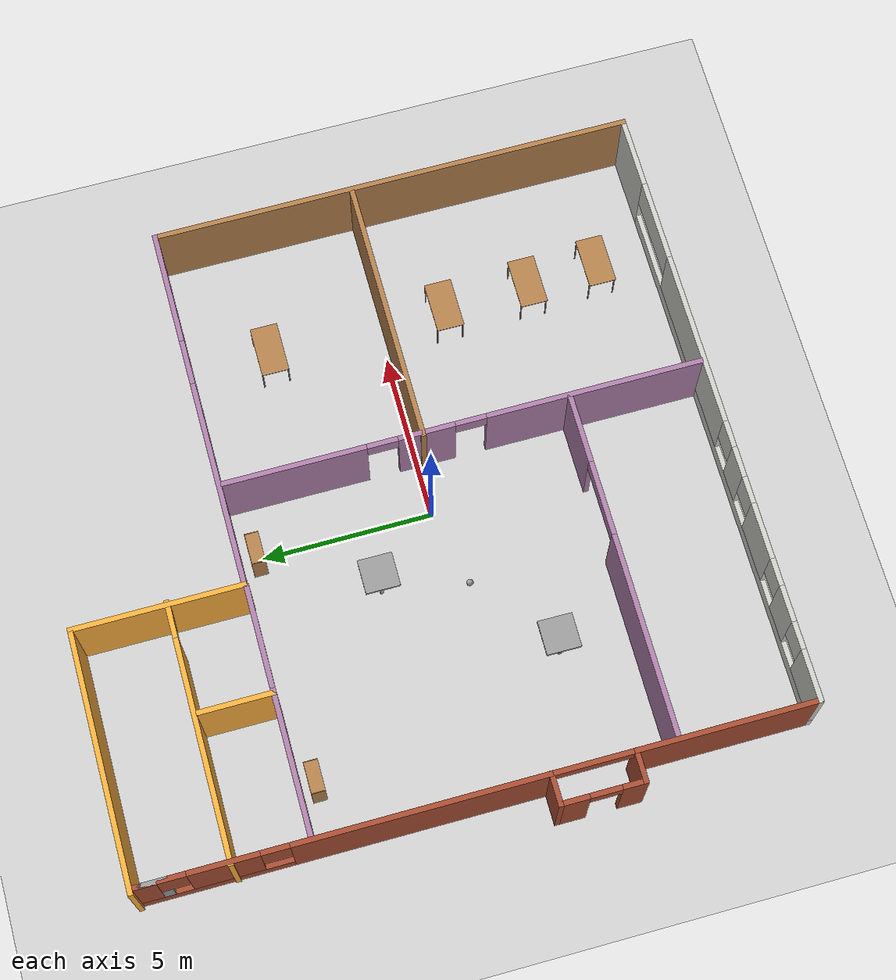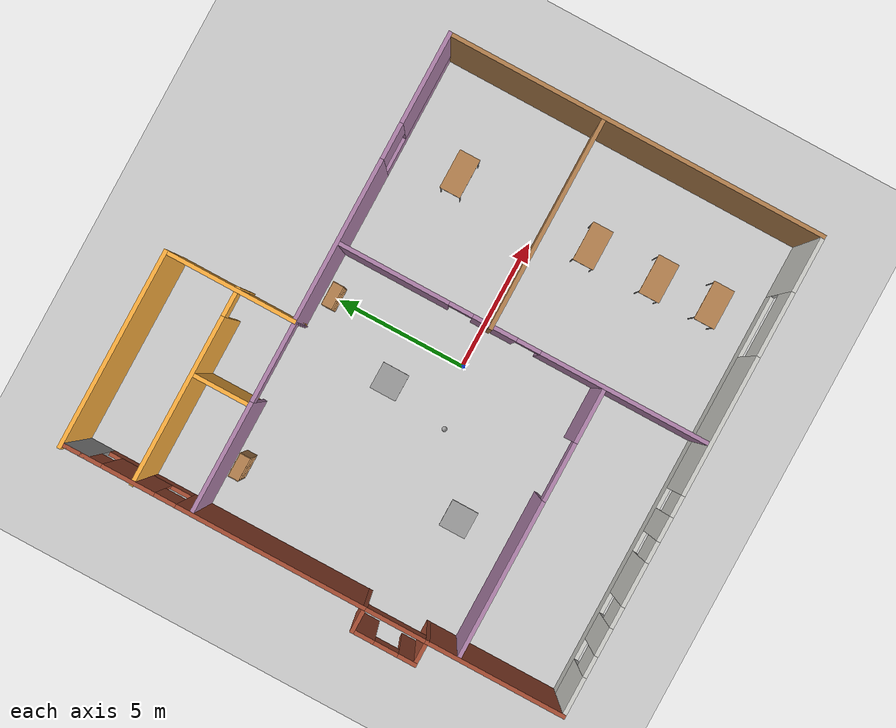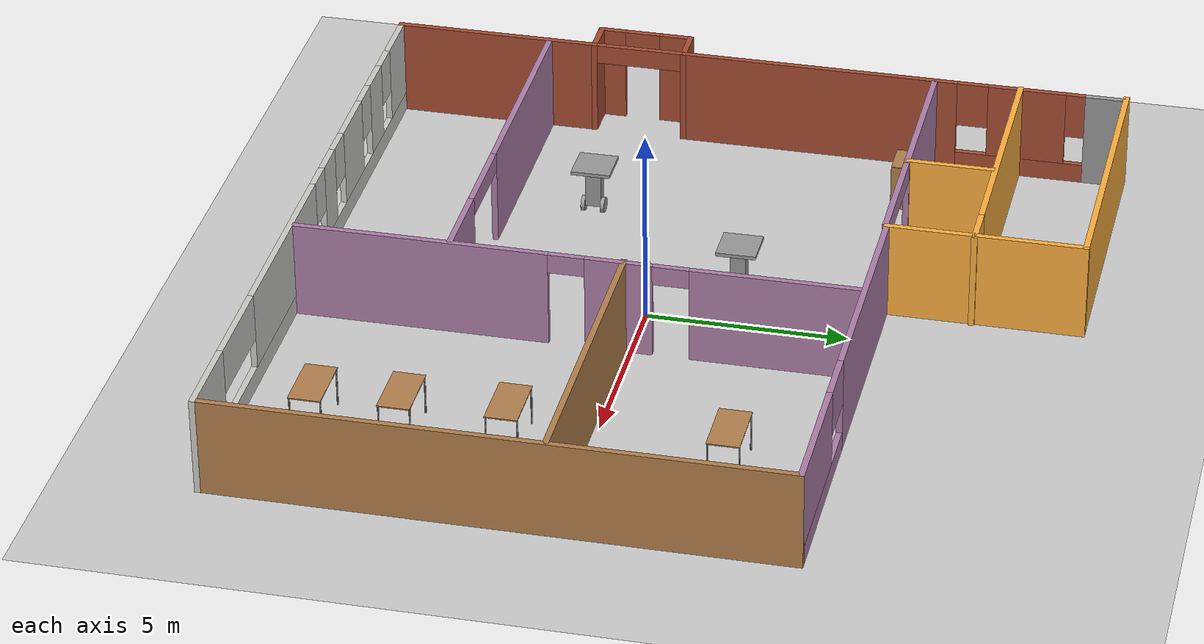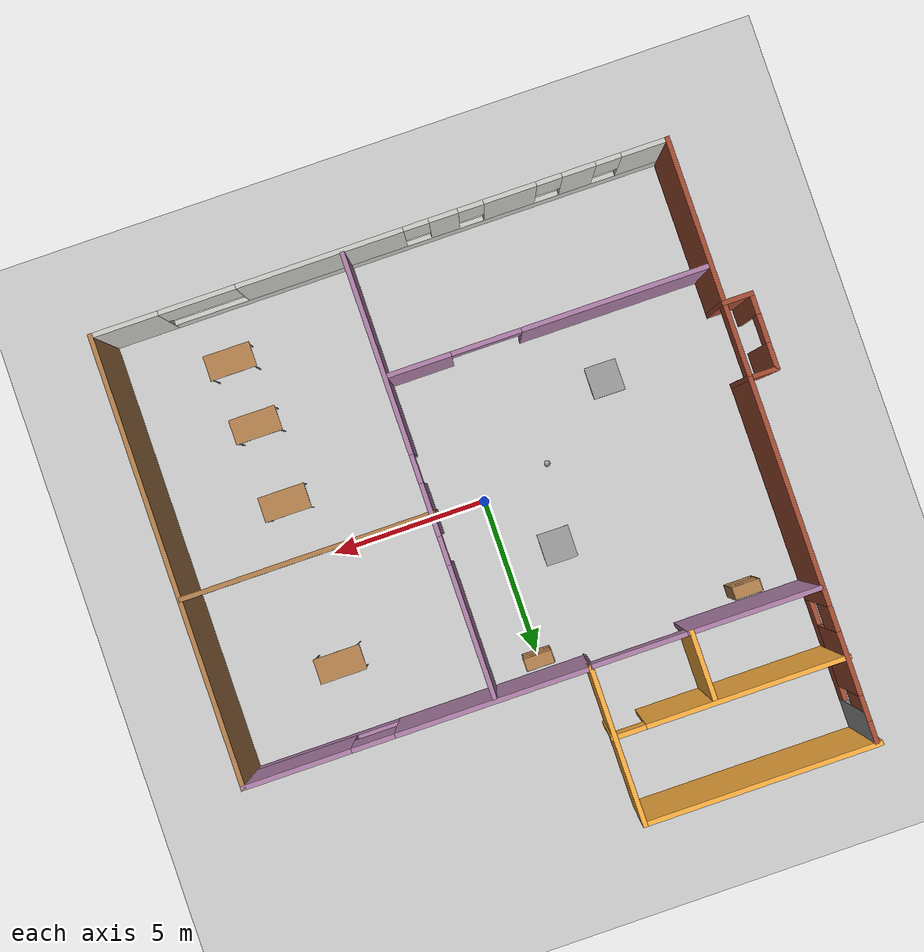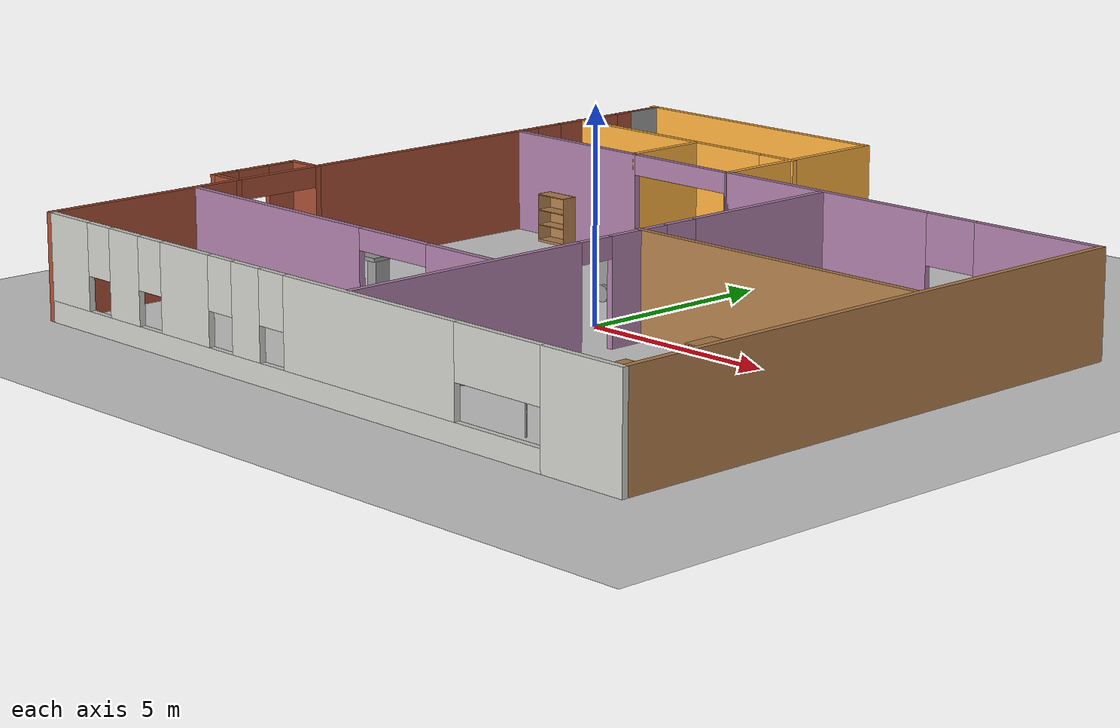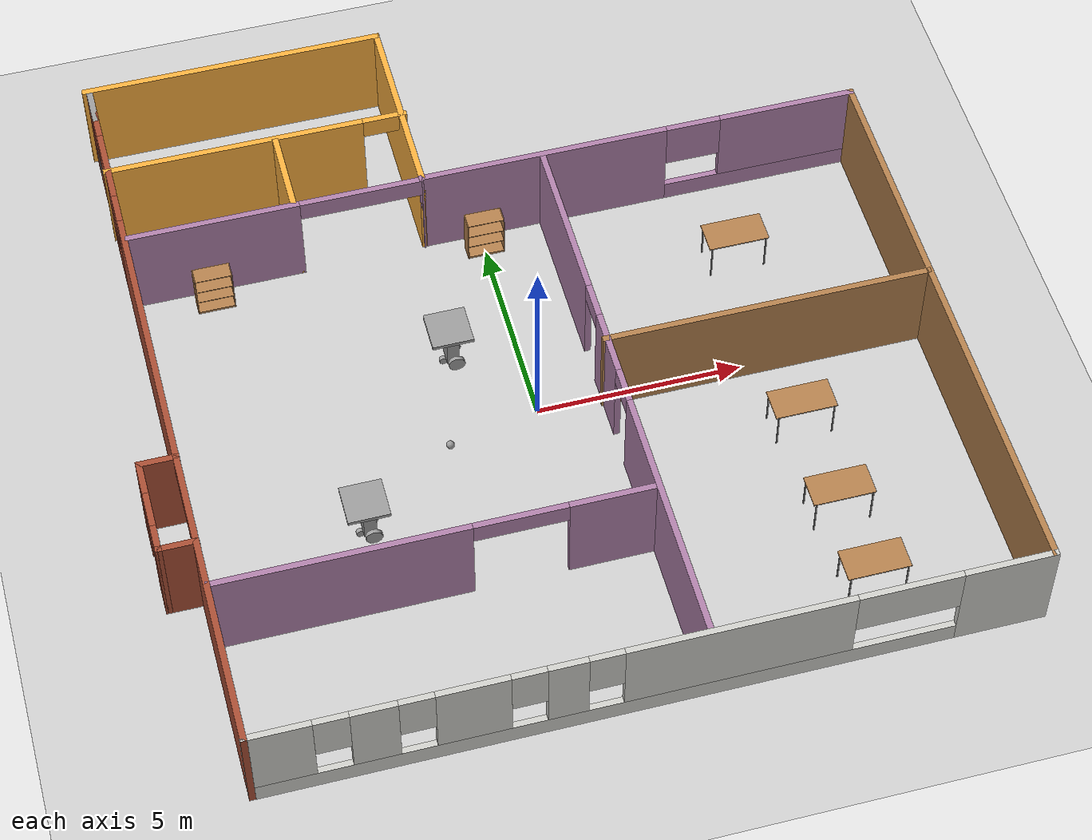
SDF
<sdf version="1.6">
 <world name="default">
  <plugin name="hello" filename="libhello.so"/>
  <light name="sun" type="directional">
   <pose>0 0 10 0 -0 0</pose>
   <diffuse>0.8 0.8 0.8 1</diffuse>
   <specular>0.2 0.2 0.2 1</specular>
   <attenuation>
    <range>1000</range>
    <constant>0.9</constant>
    <linear>0.01</linear>
    <quadratic>0.001</quadratic>
   </attenuation>
   <direction>-0.5 0.1 -0.9</direction>
  </light>
  <model name="ground_plane">
   <static>1</static>
   <link name="link">
    <collision name="collision">
     <geometry><plane><normal>0 0 1</normal><size>100 100</size></plane></geometry>
     <surface>
      <contact><collide_bitmask>65535</collide_bitmask></contact>
      <friction><ode><mu>100</mu><mu2>50</mu2></ode></friction>
     </surface>
    </collision>
    <visual name="visual">
     <cast_shadows>0</cast_shadows>
     <geometry><plane><normal>0 0 1</normal><size>100 100</size></plane></geometry>
     <material>
      <script><uri>file://media/materials/scripts/gazebo.material</uri><name>Gazebo/Grey</name></script>
     </material>
    </visual>
   </link>
  </model>
  <gravity>0 0 -9.8</gravity>
  <magnetic_field>6e-06 2.3e-05 -4.2e-05</magnetic_field>
  <atmosphere type="adiabatic"/>
  <physics name="default_physics" default="0" type="ode">
   <max_step_size>0.001</max_step_size>
   <real_time_factor>1</real_time_factor>
   <real_time_update_rate>1000</real_time_update_rate>
  </physics>
  <scene><ambient>0.4 0.4 0.4 1</ambient><background>0.7 0.7 0.7 1</background><shadows>1</shadows></scene>
  <audio><device>default</device></audio>
  <spherical_coordinates>
   <surface_model>EARTH_WGS84</surface_model>
   <latitude_deg>0</latitude_deg>
   <longitude_deg>0</longitude_deg>
   <elevation>0</elevation>
   <heading_deg>0</heading_deg>
  </spherical_coordinates>
  <model name="apartment-structure">
   <pose>-0.00459 1.0398 0 0 -0 0</pose>
   <link name="Wall_14">
    <collision name="Wall_14_Collision">
     <geometry><box><size>7.5 0.15 2.5</size></box></geometry>
     <pose>0 0 1.25 0 -0 0</pose>
    </collision>
    <visual name="Wall_14_Visual">
     <pose>0 0 1.25 0 -0 0</pose>
     <geometry><box><size>7.5 0.15 2.5</size></box></geometry>
     <material>
      <script><uri>file://media/materials/scripts/gazebo.material</uri><name>Gazebo/Grey</name></script>
      <ambient>0.988235 0.686275 0.243137 1</ambient>
     </material>
     <meta><layer>0</layer></meta>
    </visual>
    <pose>-5.05241 9.475 0 0 -0 0</pose>
   </link>
   <link name="Wall_15">
    <collision name="Wall_15_Collision">
     <geometry><box><size>5 0.15 2.5</size></box></geometry>
     <pose>0 0 1.25 0 -0 0</pose>
    </collision>
    <visual name="Wall_15_Visual">
     <pose>0 0 1.25 0 -0 0</pose>
     <geometry><box><size>5 0.15 2.5</size></box></geometry>
     <material>
      <script><uri>file://media/materials/scripts/gazebo.material</uri><name>Gazebo/Grey</name></script>
      <ambient>0.988235 0.686275 0.243137 1</ambient>
     </material>
     <meta><layer>0</layer></meta>
    </visual>
    <pose>-1.37741 7.05 0 0 -0 -1.5708</pose>
   </link>
   <link name="Wall_16">
    <pose>4.0476 4.625 0 0 -0 0</pose>
    <visual name="Wall_16_Visual_0">
     <pose>-2.39955 0 1.25 0 -0 0</pose>
     <geometry><box><size>6.20089 0.15 2.5</size></box></geometry>
     <material>
      <script><uri>file://media/materials/scripts/gazebo.material</uri><name>Gazebo/Grey</name></script>
      <ambient>0.678431 0.498039 0.658824 1</ambient>
     </material>
     <meta><layer>0</layer></meta>
    </visual>
    <collision name="Wall_16_Collision_0">
     <geometry><box><size>6.20089 0.15 2.5</size></box></geometry>
     <pose>-2.39955 0 1.25 0 -0 0</pose>
    </collision>
    <visual name="Wall_16_Visual_1">
     <pose>3.10045 0 0.25 0 -0 0</pose>
     <geometry><box><size>4.79911 0.15 0.5</size></box></geometry>
     <material>
      <script><uri>file://media/materials/scripts/gazebo.material</uri><name>Gazebo/Grey</name></script>
      <ambient>0.678431 0.498039 0.658824 1</ambient>
     </material>
     <meta><layer>0</layer></meta>
    </visual>
    <collision name="Wall_16_Collision_1">
     <geometry><box><size>4.79911 0.15 0.5</size></box></geometry>
     <pose>3.10045 0 0.25 0 -0 0</pose>
    </collision>
    <visual name="Wall_16_Visual_2">
     <pose>3.77959 0 1.5 0 -0 0</pose>
     <geometry><box><size>3.44082 0.15 2</size></box></geometry>
     <material>
      <script><uri>file://media/materials/scripts/gazebo.material</uri><name>Gazebo/Grey</name></script>
      <ambient>0.678431 0.498039 0.658824 1</ambient>
     </material>
     <meta><layer>0</layer></meta>
    </visual>
    <collision name="Wall_16_Collision_2">
     <geometry><box><size>3.44082 0.15 2</size></box></geometry>
     <pose>3.77959 0 1.5 0 -0 0</pose>
    </collision>
    <visual name="Wall_16_Visual_3">
     <pose>1.38003 0 1.9 0 -0 0</pose>
     <geometry><box><size>1.35829 0.15 1.2</size></box></geometry>
     <material>
      <script><uri>file://media/materials/scripts/gazebo.material</uri><name>Gazebo/Grey</name></script>
      <ambient>0.678431 0.498039 0.658824 1</ambient>
     </material>
     <meta><layer>0</layer></meta>
    </visual>
    <collision name="Wall_16_Collision_3">
     <geometry><box><size>1.35829 0.15 1.2</size></box></geometry>
     <pose>1.38003 0 1.9 0 -0 0</pose>
    </collision>
   </link>
   <link name="Wall_18">
    <collision name="Wall_18_Collision">
     <geometry><box><size>14.25 0.15 2.5</size></box></geometry>
     <pose>0 0 1.25 0 -0 0</pose>
    </collision>
    <visual name="Wall_18_Visual">
     <pose>0 0 1.25 0 -0 0</pose>
     <geometry><box><size>14.25 0.15 2.5</size></box></geometry>
     <material>
      <script><uri>file://media/materials/scripts/gazebo.material</uri><name>Gazebo/Wood</name></script>
      <ambient>1 1 1 1</ambient>
     </material>
     <meta><layer>0</layer></meta>
    </visual>
    <pose>9.47259 -2.425 0 0 -0 -1.5708</pose>
   </link>
   <link name="Wall_19">
    <pose>0.422594 -9.475 0 0 -0 3.14159</pose>
    <visual name="Wall_19_Visual_0">
     <pose>-8.03266 0 1.25 0 -0 0</pose>
     <geometry><box><size>2.18468 0.15 2.5</size></box></geometry>
     <material>
      <script><uri>file://media/materials/scripts/gazebo.material</uri><name>Gazebo/CeilingTiled</name></script>
      <ambient>1 1 1 1</ambient>
     </material>
     <meta><layer>0</layer></meta>
    </visual>
    <collision name="Wall_19_Collision_0">
     <geometry><box><size>2.18468 0.15 2.5</size></box></geometry>
     <pose>-8.03266 0 1.25 0 -0 0</pose>
    </collision>
    <visual name="Wall_19_Visual_1">
     <pose>1.09234 0 0.25 0 -0 0</pose>
     <geometry><box><size>16.0653 0.15 0.5</size></box></geometry>
     <material>
      <script><uri>file://media/materials/scripts/gazebo.material</uri><name>Gazebo/CeilingTiled</name></script>
      <ambient>1 1 1 1</ambient>
     </material>
     <meta><layer>0</layer></meta>
    </visual>
    <collision name="Wall_19_Collision_1">
     <geometry><box><size>16.0653 0.15 0.5</size></box></geometry>
     <pose>1.09234 0 0.25 0 -0 0</pose>
    </collision>
    <visual name="Wall_19_Visual_2">
     <pose>-1.88793 0 1.5 0 -0 0</pose>
     <geometry><box><size>5.24811 0.15 2</size></box></geometry>
     <material>
      <script><uri>file://media/materials/scripts/gazebo.material</uri><name>Gazebo/CeilingTiled</name></script>
      <ambient>1 1 1 1</ambient>
     </material>
     <meta><layer>0</layer></meta>
    </visual>
    <collision name="Wall_19_Collision_2">
     <geometry><box><size>5.24811 0.15 2</size></box></geometry>
     <pose>-1.88793 0 1.5 0 -0 0</pose>
    </collision>
    <visual name="Wall_19_Visual_3">
     <pose>1.99682 0 1.5 0 -0 0</pose>
     <geometry><box><size>0.921385 0.15 2</size></box></geometry>
     <material>
      <script><uri>file://media/materials/scripts/gazebo.material</uri><name>Gazebo/CeilingTiled</name></script>
      <ambient>1 1 1 1</ambient>
     </material>
     <meta><layer>0</layer></meta>
    </visual>
    <collision name="Wall_19_Collision_3">
     <geometry><box><size>0.921385 0.15 2</size></box></geometry>
     <pose>1.99682 0 1.5 0 -0 0</pose>
    </collision>
    <visual name="Wall_19_Visual_4">
     <pose>4.09039 0 1.5 0 -0 0</pose>
     <geometry><box><size>1.66577 0.15 2</size></box></geometry>
     <material>
      <script><uri>file://media/materials/scripts/gazebo.material</uri><name>Gazebo/CeilingTiled</name></script>
      <ambient>1 1 1 1</ambient>
     </material>
     <meta><layer>0</layer></meta>
    </visual>
    <collision name="Wall_19_Collision_4">
     <geometry><box><size>1.66577 0.15 2</size></box></geometry>
     <pose>4.09039 0 1.5 0 -0 0</pose>
    </collision>
    <visual name="Wall_19_Visual_5">
     <pose>6.25375 0 1.5 0 -0 0</pose>
     <geometry><box><size>1.06096 0.15 2</size></box></geometry>
     <material>
      <script><uri>file://media/materials/scripts/gazebo.material</uri><name>Gazebo/CeilingTiled</name></script>
      <ambient>1 1 1 1</ambient>
     </material>
     <meta><layer>0</layer></meta>
    </visual>
    <collision name="Wall_19_Collision_5">
     <geometry><box><size>1.06096 0.15 2</size></box></geometry>
     <pose>6.25375 0 1.5 0 -0 0</pose>
    </collision>
    <visual name="Wall_19_Visual_6">
     <pose>8.35462 0 1.5 0 -0 0</pose>
     <geometry><box><size>1.54077 0.15 2</size></box></geometry>
     <material>
      <script><uri>file://media/materials/scripts/gazebo.material</uri><name>Gazebo/CeilingTiled</name></script>
      <ambient>1 1 1 1</ambient>
     </material>
     <meta><layer>0</layer></meta>
    </visual>
    <collision name="Wall_19_Collision_6">
     <geometry><box><size>1.54077 0.15 2</size></box></geometry>
     <pose>8.35462 0 1.5 0 -0 0</pose>
    </collision>
    <visual name="Wall_19_Visual_7">
     <pose>-5.72615 0 1.9 0 -0 0</pose>
     <geometry><box><size>2.42834 0.15 1.2</size></box></geometry>
     <material>
      <script><uri>file://media/materials/scripts/gazebo.material</uri><name>Gazebo/CeilingTiled</name></script>
      <ambient>1 1 1 1</ambient>
     </material>
     <meta><layer>0</layer></meta>
    </visual>
    <collision name="Wall_19_Collision_7">
     <geometry><box><size>2.42834 0.15 1.2</size></box></geometry>
     <pose>-5.72615 0 1.9 0 -0 0</pose>
    </collision>
    <visual name="Wall_19_Visual_8">
     <pose>1.13612 0 1.9 0 -0 0</pose>
     <geometry><box><size>0.8 0.15 1.2</size></box></geometry>
     <material>
      <script><uri>file://media/materials/scripts/gazebo.material</uri><name>Gazebo/CeilingTiled</name></script>
      <ambient>1 1 1 1</ambient>
     </material>
     <meta><layer>0</layer></meta>
    </visual>
    <collision name="Wall_19_Collision_8">
     <geometry><box><size>0.8 0.15 1.2</size></box></geometry>
     <pose>1.13612 0 1.9 0 -0 0</pose>
    </collision>
    <visual name="Wall_19_Visual_9">
     <pose>2.85751 0 1.9 0 -0 0</pose>
     <geometry><box><size>0.8 0.15 1.2</size></box></geometry>
     <material>
      <script><uri>file://media/materials/scripts/gazebo.material</uri><name>Gazebo/CeilingTiled</name></script>
      <ambient>1 1 1 1</ambient>
     </material>
     <meta><layer>0</layer></meta>
    </visual>
    <collision name="Wall_19_Collision_9">
     <geometry><box><size>0.8 0.15 1.2</size></box></geometry>
     <pose>2.85751 0 1.9 0 -0 0</pose>
    </collision>
    <visual name="Wall_19_Visual_10">
     <pose>5.32328 0 1.9 0 -0 0</pose>
     <geometry><box><size>0.8 0.15 1.2</size></box></geometry>
     <material>
      <script><uri>file://media/materials/scripts/gazebo.material</uri><name>Gazebo/CeilingTiled</name></script>
      <ambient>1 1 1 1</ambient>
     </material>
     <meta><layer>0</layer></meta>
    </visual>
    <collision name="Wall_19_Collision_10">
     <geometry><box><size>0.8 0.15 1.2</size></box></geometry>
     <pose>5.32328 0 1.9 0 -0 0</pose>
    </collision>
    <visual name="Wall_19_Visual_11">
     <pose>7.18423 0 1.9 0 -0 0</pose>
     <geometry><box><size>0.8 0.15 1.2</size></box></geometry>
     <material>
      <script><uri>file://media/materials/scripts/gazebo.material</uri><name>Gazebo/CeilingTiled</name></script>
      <ambient>1 1 1 1</ambient>
     </material>
     <meta><layer>0</layer></meta>
    </visual>
    <collision name="Wall_19_Collision_11">
     <geometry><box><size>0.8 0.15 1.2</size></box></geometry>
     <pose>7.18423 0 1.9 0 -0 0</pose>
    </collision>
   </link>
   <link name="Wall_20">
    <pose>-8.62741 -0.049999 0 0 -0 1.5708</pose>
    <visual name="Wall_20_Visual_0">
     <pose>-6.85379 0 1.25 0 -0 0</pose>
     <geometry><box><size>5.29242 0.15 2.5</size></box></geometry>
     <material>
      <script><uri>file://media/materials/scripts/gazebo.material</uri><name>Gazebo/Bricks</name></script>
      <ambient>0.678431 0.498039 0.658824 1</ambient>
     </material>
     <meta><layer>0</layer></meta>
    </visual>
    <collision name="Wall_20_Collision_0">
     <geometry><box><size>5.29242 0.15 2.5</size></box></geometry>
     <pose>-6.85379 0 1.25 0 -0 0</pose>
    </collision>
    <visual name="Wall_20_Visual_1">
     <pose>1.6293 0 1.25 0 -0 0</pose>
     <geometry><box><size>7.17537 0.15 2.5</size></box></geometry>
     <material>
      <script><uri>file://media/materials/scripts/gazebo.material</uri><name>Gazebo/Bricks</name></script>
      <ambient>0.678431 0.498039 0.658824 1</ambient>
     </material>
     <meta><layer>0</layer></meta>
    </visual>
    <collision name="Wall_20_Collision_1">
     <geometry><box><size>7.17537 0.15 2.5</size></box></geometry>
     <pose>1.6293 0 1.25 0 -0 0</pose>
    </collision>
    <visual name="Wall_20_Visual_2">
     <pose>7.3585 0 0.25 0 -0 0</pose>
     <geometry><box><size>4.28301 0.15 0.5</size></box></geometry>
     <material>
      <script><uri>file://media/materials/scripts/gazebo.material</uri><name>Gazebo/Bricks</name></script>
      <ambient>0.678431 0.498039 0.658824 1</ambient>
     </material>
     <meta><layer>0</layer></meta>
    </visual>
    <collision name="Wall_20_Collision_2">
     <geometry><box><size>4.28301 0.15 0.5</size></box></geometry>
     <pose>7.3585 0 0.25 0 -0 0</pose>
    </collision>
    <visual name="Wall_20_Visual_3">
     <pose>7.01271 0 1.5 0 -0 0</pose>
     <geometry><box><size>1.99144 0.15 2</size></box></geometry>
     <material>
      <script><uri>file://media/materials/scripts/gazebo.material</uri><name>Gazebo/Bricks</name></script>
      <ambient>0.678431 0.498039 0.658824 1</ambient>
     </material>
     <meta><layer>0</layer></meta>
    </visual>
    <collision name="Wall_20_Collision_3">
     <geometry><box><size>1.99144 0.15 2</size></box></geometry>
     <pose>7.01271 0 1.5 0 -0 0</pose>
    </collision>
    <visual name="Wall_20_Visual_4">
     <pose>9.15421 0 1.5 0 -0 0</pose>
     <geometry><box><size>0.691574 0.15 2</size></box></geometry>
     <material>
      <script><uri>file://media/materials/scripts/gazebo.material</uri><name>Gazebo/Bricks</name></script>
      <ambient>0.678431 0.498039 0.658824 1</ambient>
     </material>
     <meta><layer>0</layer></meta>
    </visual>
    <collision name="Wall_20_Collision_4">
     <geometry><box><size>0.691574 0.15 2</size></box></geometry>
     <pose>9.15421 0 1.5 0 -0 0</pose>
    </collision>
    <visual name="Wall_20_Visual_5">
     <pose>5.61699 0 1.9 0 -0 0</pose>
     <geometry><box><size>0.8 0.15 1.2</size></box></geometry>
     <material>
      <script><uri>file://media/materials/scripts/gazebo.material</uri><name>Gazebo/Bricks</name></script>
      <ambient>0.678431 0.498039 0.658824 1</ambient>
     </material>
     <meta><layer>0</layer></meta>
    </visual>
    <collision name="Wall_20_Collision_5">
     <geometry><box><size>0.8 0.15 1.2</size></box></geometry>
     <pose>5.61699 0 1.9 0 -0 0</pose>
    </collision>
    <visual name="Wall_20_Visual_6">
     <pose>8.40843 0 1.9 0 -0 0</pose>
     <geometry><box><size>0.8 0.15 1.2</size></box></geometry>
     <material>
      <script><uri>file://media/materials/scripts/gazebo.material</uri><name>Gazebo/Bricks</name></script>
      <ambient>0.678431 0.498039 0.658824 1</ambient>
     </material>
     <meta><layer>0</layer></meta>
    </visual>
    <collision name="Wall_20_Collision_6">
     <geometry><box><size>0.8 0.15 1.2</size></box></geometry>
     <pose>8.40843 0 1.9 0 -0 0</pose>
    </collision>
    <visual name="Wall_20_Visual_7">
     <pose>-3.08298 0 2.25 0 -0 0</pose>
     <geometry><box><size>2.24919 0.15 0.5</size></box></geometry>
     <material>
      <script><uri>file://media/materials/scripts/gazebo.material</uri><name>Gazebo/Bricks</name></script>
      <ambient>0.678431 0.498039 0.658824 1</ambient>
     </material>
     <meta><layer>0</layer></meta>
    </visual>
    <collision name="Wall_20_Collision_7">
     <geometry><box><size>2.24919 0.15 0.5</size></box></geometry>
     <pose>-3.08298 0 2.25 0 -0 0</pose>
    </collision>
   </link>
   <link name="Wall_21">
    <collision name="Wall_21_Collision">
     <geometry><box><size>1 0.15 2.5</size></box></geometry>
     <pose>0 0 1.25 0 -0 0</pose>
    </collision>
    <visual name="Wall_21_Visual">
     <pose>0 0 1.25 0 -0 0</pose>
     <geometry><box><size>1 0.15 2.5</size></box></geometry>
     <material>
      <script><uri>file://media/materials/scripts/gazebo.material</uri><name>Gazebo/Grey</name></script>
      <ambient>1 1 1 1</ambient>
     </material>
     <meta><layer>0</layer></meta>
    </visual>
    <pose>-8.62741 8.95 0 0 -0 -1.5708</pose>
   </link>
   <link name="Wall_23">
    <pose>-4.99412 6.77661 0 0 -0 0</pose>
    <visual name="Wall_23_Visual_0">
     <pose>-0.552885 0 1.25 0 -0 0</pose>
     <geometry><box><size>6.39423 0.15 2.5</size></box></geometry>
     <material>
      <script><uri>file://media/materials/scripts/gazebo.material</uri><name>Gazebo/Grey</name></script>
      <ambient>0.988235 0.686275 0.243137 1</ambient>
     </material>
     <meta><layer>0</layer></meta>
    </visual>
    <collision name="Wall_23_Collision_0">
     <geometry><box><size>6.39423 0.15 2.5</size></box></geometry>
     <pose>-0.552885 0 1.25 0 -0 0</pose>
    </collision>
    <visual name="Wall_23_Visual_1">
     <pose>3.69364 0 1.25 0 -0 0</pose>
     <geometry><box><size>0.112723 0.15 2.5</size></box></geometry>
     <material>
      <script><uri>file://media/materials/scripts/gazebo.material</uri><name>Gazebo/Grey</name></script>
      <ambient>0.988235 0.686275 0.243137 1</ambient>
     </material>
     <meta><layer>0</layer></meta>
    </visual>
    <collision name="Wall_23_Collision_1">
     <geometry><box><size>0.112723 0.15 2.5</size></box></geometry>
     <pose>3.69364 0 1.25 0 -0 0</pose>
    </collision>
    <visual name="Wall_23_Visual_2">
     <pose>3.14075 0 2.25 0 -0 0</pose>
     <geometry><box><size>0.993048 0.15 0.5</size></box></geometry>
     <material>
      <script><uri>file://media/materials/scripts/gazebo.material</uri><name>Gazebo/Grey</name></script>
      <ambient>0.988235 0.686275 0.243137 1</ambient>
     </material>
     <meta><layer>0</layer></meta>
    </visual>
    <collision name="Wall_23_Collision_2">
     <geometry><box><size>0.993048 0.15 0.5</size></box></geometry>
     <pose>3.14075 0 2.25 0 -0 0</pose>
    </collision>
   </link>
   <link name="Wall_26">
    <pose>-4.98544 4.58357 0 0 -0 3.14159</pose>
    <visual name="Wall_26_Visual_0">
     <pose>-3.60354 0 1.25 0 -0 0</pose>
     <geometry><box><size>0.042923 0.15 2.5</size></box></geometry>
     <material>
      <script><uri>file://media/materials/scripts/gazebo.material</uri><name>Gazebo/Grey</name></script>
      <ambient>0.678431 0.498039 0.658824 1</ambient>
     </material>
     <meta><layer>0</layer></meta>
    </visual>
    <collision name="Wall_26_Collision_0">
     <geometry><box><size>0.042923 0.15 2.5</size></box></geometry>
     <pose>-3.60354 0 1.25 0 -0 0</pose>
    </collision>
    <visual name="Wall_26_Visual_1">
     <pose>1.51825 0 1.25 0 -0 0</pose>
     <geometry><box><size>4.2135 0.15 2.5</size></box></geometry>
     <material>
      <script><uri>file://media/materials/scripts/gazebo.material</uri><name>Gazebo/Grey</name></script>
      <ambient>0.678431 0.498039 0.658824 1</ambient>
     </material>
     <meta><layer>0</layer></meta>
    </visual>
    <collision name="Wall_26_Collision_1">
     <geometry><box><size>4.2135 0.15 2.5</size></box></geometry>
     <pose>1.51825 0 1.25 0 -0 0</pose>
    </collision>
    <visual name="Wall_26_Visual_2">
     <pose>-2.08529 0 2.25 0 -0 0</pose>
     <geometry><box><size>2.99358 0.15 0.5</size></box></geometry>
     <material>
      <script><uri>file://media/materials/scripts/gazebo.material</uri><name>Gazebo/Grey</name></script>
      <ambient>0.678431 0.498039 0.658824 1</ambient>
     </material>
     <meta><layer>0</layer></meta>
    </visual>
    <collision name="Wall_26_Collision_2">
     <geometry><box><size>2.99358 0.15 0.5</size></box></geometry>
     <pose>-2.08529 0 2.25 0 -0 0</pose>
    </collision>
   </link>
   <link name="Wall_28">
    <collision name="Wall_28_Collision">
     <geometry><box><size>2.25 0.15 2.5</size></box></geometry>
     <pose>0 0 1.25 0 -0 0</pose>
    </collision>
    <visual name="Wall_28_Visual">
     <pose>0 0 1.25 0 -0 0</pose>
     <geometry><box><size>2.25 0.15 2.5</size></box></geometry>
     <material>
      <script><uri>file://media/materials/scripts/gazebo.material</uri><name>Gazebo/Grey</name></script>
      <ambient>0.988235 0.686275 0.243137 1</ambient>
     </material>
     <meta><layer>0</layer></meta>
    </visual>
    <pose>-4.52849 5.63357 0 0 -0 -1.5708</pose>
   </link>
   <link name="Wall_30">
    <pose>1.61267 -2.42806 0 0 -0 -1.5708</pose>
    <visual name="Wall_30_Visual_0">
     <pose>-4.90783 0 1.25 0 -0 0</pose>
     <geometry><box><size>4.18434 0.15 2.5</size></box></geometry>
     <material>
      <script><uri>file://media/materials/scripts/gazebo.material</uri><name>Gazebo/Grey</name></script>
      <ambient>0.678431 0.498039 0.658824 1</ambient>
     </material>
     <meta><layer>0</layer></meta>
    </visual>
    <collision name="Wall_30_Collision_0">
     <geometry><box><size>4.18434 0.15 2.5</size></box></geometry>
     <pose>-4.90783 0 1.25 0 -0 0</pose>
    </collision>
    <visual name="Wall_30_Visual_1">
     <pose>-1.08625 0 1.25 0 -0 0</pose>
     <geometry><box><size>1.65881 0.15 2.5</size></box></geometry>
     <material>
      <script><uri>file://media/materials/scripts/gazebo.material</uri><name>Gazebo/Grey</name></script>
      <ambient>0.678431 0.498039 0.658824 1</ambient>
     </material>
     <meta><layer>0</layer></meta>
    </visual>
    <collision name="Wall_30_Collision_1">
     <geometry><box><size>1.65881 0.15 2.5</size></box></geometry>
     <pose>-1.08625 0 1.25 0 -0 0</pose>
    </collision>
    <visual name="Wall_30_Visual_2">
     <pose>3.82158 0 1.25 0 -0 0</pose>
     <geometry><box><size>6.35684 0.15 2.5</size></box></geometry>
     <material>
      <script><uri>file://media/materials/scripts/gazebo.material</uri><name>Gazebo/Grey</name></script>
      <ambient>0.678431 0.498039 0.658824 1</ambient>
     </material>
     <meta><layer>0</layer></meta>
    </visual>
    <collision name="Wall_30_Collision_2">
     <geometry><box><size>6.35684 0.15 2.5</size></box></geometry>
     <pose>3.82158 0 1.25 0 -0 0</pose>
    </collision>
    <visual name="Wall_30_Visual_3">
     <pose>-2.36566 0 2.25 0 -0 0</pose>
     <geometry><box><size>0.9 0.15 0.5</size></box></geometry>
     <material>
      <script><uri>file://media/materials/scripts/gazebo.material</uri><name>Gazebo/Grey</name></script>
      <ambient>0.678431 0.498039 0.658824 1</ambient>
     </material>
     <meta><layer>0</layer></meta>
    </visual>
    <collision name="Wall_30_Collision_3">
     <geometry><box><size>0.9 0.15 0.5</size></box></geometry>
     <pose>-2.36566 0 2.25 0 -0 0</pose>
    </collision>
    <visual name="Wall_30_Visual_4">
     <pose>0.193159 0 2.25 0 -0 0</pose>
     <geometry><box><size>0.9 0.15 0.5</size></box></geometry>
     <material>
      <script><uri>file://media/materials/scripts/gazebo.material</uri><name>Gazebo/Grey</name></script>
      <ambient>0.678431 0.498039 0.658824 1</ambient>
     </material>
     <meta><layer>0</layer></meta>
    </visual>
    <collision name="Wall_30_Collision_4">
     <geometry><box><size>0.9 0.15 0.5</size></box></geometry>
     <pose>0.193159 0 2.25 0 -0 0</pose>
    </collision>
   </link>
   <link name="Wall_32">
    <pose>-3.52607 -5.5057 0 0 -0 0</pose>
    <visual name="Wall_32_Visual_0">
     <pose>-2.13724 0 1.25 0 -0 0</pose>
     <geometry><box><size>5.97551 0.15 2.5</size></box></geometry>
     <material>
      <script><uri>file://media/materials/scripts/gazebo.material</uri><name>Gazebo/Grey</name></script>
      <ambient>0.678431 0.498039 0.658824 1</ambient>
     </material>
     <meta><layer>0</layer></meta>
    </visual>
    <collision name="Wall_32_Collision_0">
     <geometry><box><size>5.97551 0.15 2.5</size></box></geometry>
     <pose>-2.13724 0 1.25 0 -0 0</pose>
    </collision>
    <visual name="Wall_32_Visual_1">
     <pose>4.08909 0 1.25 0 -0 0</pose>
     <geometry><box><size>2.07182 0.15 2.5</size></box></geometry>
     <material>
      <script><uri>file://media/materials/scripts/gazebo.material</uri><name>Gazebo/Grey</name></script>
      <ambient>0.678431 0.498039 0.658824 1</ambient>
     </material>
     <meta><layer>0</layer></meta>
    </visual>
    <collision name="Wall_32_Collision_1">
     <geometry><box><size>2.07182 0.15 2.5</size></box></geometry>
     <pose>4.08909 0 1.25 0 -0 0</pose>
    </collision>
    <visual name="Wall_32_Visual_2">
     <pose>1.95185 0 2.25 0 -0 0</pose>
     <geometry><box><size>2.20267 0.15 0.5</size></box></geometry>
     <material>
      <script><uri>file://media/materials/scripts/gazebo.material</uri><name>Gazebo/Grey</name></script>
      <ambient>0.678431 0.498039 0.658824 1</ambient>
     </material>
     <meta><layer>0</layer></meta>
    </visual>
    <collision name="Wall_32_Collision_2">
     <geometry><box><size>2.20267 0.15 0.5</size></box></geometry>
     <pose>1.95185 0 2.25 0 -0 0</pose>
    </collision>
   </link>
   <link name="Wall_34">
    <collision name="Wall_34_Collision">
     <geometry><box><size>8 0.15 2.5</size></box></geometry>
     <pose>0 0 1.25 0 -0 0</pose>
    </collision>
    <visual name="Wall_34_Visual">
     <pose>0 0 1.25 0 -0 0</pose>
     <geometry><box><size>8 0.15 2.5</size></box></geometry>
     <material>
      <script><uri>file://media/materials/scripts/gazebo.material</uri><name>Gazebo/Wood</name></script>
      <ambient>1 1 1 1</ambient>
     </material>
     <meta><layer>0</layer></meta>
    </visual>
    <pose>5.49114 -1.2255 0 0 -0 0</pose>
   </link>
   <link name="Wall_36">
    <collision name="Wall_36_Collision">
     <geometry><box><size>1 0.15 2.5</size></box></geometry>
     <pose>0 0 1.25 0 -0 0</pose>
    </collision>
    <visual name="Wall_36_Visual">
     <pose>0 0 1.25 0 -0 0</pose>
     <geometry><box><size>1 0.15 2.5</size></box></geometry>
     <material>
      <script><uri>file://media/materials/scripts/gazebo.material</uri><name>Gazebo/Bricks</name></script>
      <ambient>1 1 1 1</ambient>
     </material>
     <meta><layer>0</layer></meta>
    </visual>
    <pose>-9.04759 -1.96988 0 0 -0 3.14159</pose>
   </link>
   <link name="Wall_37">
    <pose>-9.47259 -3.14488 0 0 -0 -1.5708</pose>
    <visual name="Wall_37_Visual_0">
     <pose>-0.809427 0 1.25 0 -0 0</pose>
     <geometry><box><size>0.881146 0.15 2.5</size></box></geometry>
     <material>
      <script><uri>file://media/materials/scripts/gazebo.material</uri><name>Gazebo/Bricks</name></script>
      <ambient>1 1 1 1</ambient>
     </material>
     <meta><layer>0</layer></meta>
    </visual>
    <collision name="Wall_37_Collision_0">
     <geometry><box><size>0.881146 0.15 2.5</size></box></geometry>
     <pose>-0.809427 0 1.25 0 -0 0</pose>
    </collision>
    <visual name="Wall_37_Visual_1">
     <pose>0.890573 0 1.25 0 -0 0</pose>
     <geometry><box><size>0.718854 0.15 2.5</size></box></geometry>
     <material>
      <script><uri>file://media/materials/scripts/gazebo.material</uri><name>Gazebo/Bricks</name></script>
      <ambient>1 1 1 1</ambient>
     </material>
     <meta><layer>0</layer></meta>
    </visual>
    <collision name="Wall_37_Collision_1">
     <geometry><box><size>0.718854 0.15 2.5</size></box></geometry>
     <pose>0.890573 0 1.25 0 -0 0</pose>
    </collision>
    <visual name="Wall_37_Visual_2">
     <pose>0.081146 0 2.25 0 -0 0</pose>
     <geometry><box><size>0.9 0.15 0.5</size></box></geometry>
     <material>
      <script><uri>file://media/materials/scripts/gazebo.material</uri><name>Gazebo/Bricks</name></script>
      <ambient>1 1 1 1</ambient>
     </material>
     <meta><layer>0</layer></meta>
    </visual>
    <collision name="Wall_37_Collision_2">
     <geometry><box><size>0.9 0.15 0.5</size></box></geometry>
     <pose>0.081146 0 2.25 0 -0 0</pose>
    </collision>
   </link>
   <link name="Wall_38">
    <collision name="Wall_38_Collision">
     <geometry><box><size>1 0.15 2.5</size></box></geometry>
     <pose>0 0 1.25 0 -0 0</pose>
    </collision>
    <visual name="Wall_38_Visual">
     <pose>0 0 1.25 0 -0 0</pose>
     <geometry><box><size>1 0.15 2.5</size></box></geometry>
     <material>
      <script><uri>file://media/materials/scripts/gazebo.material</uri><name>Gazebo/Bricks</name></script>
      <ambient>1 1 1 1</ambient>
     </material>
     <meta><layer>0</layer></meta>
    </visual>
    <pose>-9.04759 -4.31988 0 0 -0 0</pose>
   </link>
   <static>1</static>
  </model>
  <model name="table">
   <static>1</static>
   <link name="link">
    <collision name="surface">
     <pose>0 0 1 0 -0 0</pose>
     <geometry><box><size>1.5 0.8 0.03</size></box></geometry>
     <surface><friction><ode><mu>0.6</mu><mu2>0.6</mu2></ode></friction></surface>
    </collision>
    <visual name="visual1">
     <pose>0 0 1 0 -0 0</pose>
     <geometry><box><size>1.5 0.8 0.03</size></box></geometry>
     <material>
      <script><uri>file://media/materials/scripts/gazebo.material</uri><name>Gazebo/Wood</name></script>
     </material>
    </visual>
    <collision name="front_left_leg">
     <pose>0.68 0.38 0.5 0 -0 0</pose>
     <geometry><cylinder><radius>0.02</radius><length>1</length></cylinder></geometry>
    </collision>
    <visual name="front_left_leg">
     <pose>0.68 0.38 0.5 0 -0 0</pose>
     <geometry><cylinder><radius>0.02</radius><length>1</length></cylinder></geometry>
     <material>
      <script><uri>file://media/materials/scripts/gazebo.material</uri><name>Gazebo/Grey</name></script>
     </material>
    </visual>
    <collision name="front_right_leg">
     <pose>0.68 -0.38 0.5 0 -0 0</pose>
     <geometry><cylinder><radius>0.02</radius><length>1</length></cylinder></geometry>
    </collision>
    <visual name="front_right_leg">
     <pose>0.68 -0.38 0.5 0 -0 0</pose>
     <geometry><cylinder><radius>0.02</radius><length>1</length></cylinder></geometry>
     <material>
      <script><uri>file://media/materials/scripts/gazebo.material</uri><name>Gazebo/Grey</name></script>
     </material>
    </visual>
    <collision name="back_right_leg">
     <pose>-0.68 -0.38 0.5 0 -0 0</pose>
     <geometry><cylinder><radius>0.02</radius><length>1</length></cylinder></geometry>
    </collision>
    <visual name="back_right_leg">
     <pose>-0.68 -0.38 0.5 0 -0 0</pose>
     <geometry><cylinder><radius>0.02</radius><length>1</length></cylinder></geometry>
     <material>
      <script><uri>file://media/materials/scripts/gazebo.material</uri><name>Gazebo/Grey</name></script>
     </material>
    </visual>
    <collision name="back_left_leg">
     <pose>-0.68 0.38 0.5 0 -0 0</pose>
     <geometry><cylinder><radius>0.02</radius><length>1</length></cylinder></geometry>
    </collision>
    <visual name="back_left_leg">
     <pose>-0.68 0.38 0.5 0 -0 0</pose>
     <geometry><cylinder><radius>0.02</radius><length>1</length></cylinder></geometry>
     <material>
      <script><uri>file://media/materials/scripts/gazebo.material</uri><name>Gazebo/Grey</name></script>
     </material>
    </visual>
   </link>
   <pose>5.83056 3.2809 0 0 -0 0</pose>
  </model>
  <model name="table_clone">
   <static>1</static>
   <link name="link">
    <collision name="surface">
     <pose>0 0 1 0 -0 0</pose>
     <geometry><box><size>1.5 0.8 0.03</size></box></geometry>
     <surface><friction><ode><mu>0.6</mu><mu2>0.6</mu2></ode></friction></surface>
    </collision>
    <visual name="visual1">
     <pose>0 0 1 0 -0 0</pose>
     <geometry><box><size>1.5 0.8 0.03</size></box></geometry>
     <material>
      <script><uri>file://media/materials/scripts/gazebo.material</uri><name>Gazebo/Wood</name></script>
     </material>
    </visual>
    <collision name="front_left_leg">
     <pose>0.68 0.38 0.5 0 -0 0</pose>
     <geometry><cylinder><radius>0.02</radius><length>1</length></cylinder></geometry>
    </collision>
    <visual name="front_left_leg">
     <pose>0.68 0.38 0.5 0 -0 0</pose>
     <geometry><cylinder><radius>0.02</radius><length>1</length></cylinder></geometry>
     <material>
      <script><uri>file://media/materials/scripts/gazebo.material</uri><name>Gazebo/Grey</name></script>
     </material>
    </visual>
    <collision name="front_right_leg">
     <pose>0.68 -0.38 0.5 0 -0 0</pose>
     <geometry><cylinder><radius>0.02</radius><length>1</length></cylinder></geometry>
    </collision>
    <visual name="front_right_leg">
     <pose>0.68 -0.38 0.5 0 -0 0</pose>
     <geometry><cylinder><radius>0.02</radius><length>1</length></cylinder></geometry>
     <material>
      <script><uri>file://media/materials/scripts/gazebo.material</uri><name>Gazebo/Grey</name></script>
     </material>
    </visual>
    <collision name="back_right_leg">
     <pose>-0.68 -0.38 0.5 0 -0 0</pose>
     <geometry><cylinder><radius>0.02</radius><length>1</length></cylinder></geometry>
    </collision>
    <visual name="back_right_leg">
     <pose>-0.68 -0.38 0.5 0 -0 0</pose>
     <geometry><cylinder><radius>0.02</radius><length>1</length></cylinder></geometry>
     <material>
      <script><uri>file://media/materials/scripts/gazebo.material</uri><name>Gazebo/Grey</name></script>
     </material>
    </visual>
    <collision name="back_left_leg">
     <pose>-0.68 0.38 0.5 0 -0 0</pose>
     <geometry><cylinder><radius>0.02</radius><length>1</length></cylinder></geometry>
    </collision>
    <visual name="back_left_leg">
     <pose>-0.68 0.38 0.5 0 -0 0</pose>
     <geometry><cylinder><radius>0.02</radius><length>1</length></cylinder></geometry>
     <material>
      <script><uri>file://media/materials/scripts/gazebo.material</uri><name>Gazebo/Grey</name></script>
     </material>
    </visual>
   </link>
   <pose>5.84228 -1.97763 0 0 -0 0</pose>
  </model>
  <model name="table_clone_0">
   <static>1</static>
   <link name="link">
    <collision name="surface">
     <pose>0 0 1 0 -0 0</pose>
     <geometry><box><size>1.5 0.8 0.03</size></box></geometry>
     <surface><friction><ode><mu>0.6</mu><mu2>0.6</mu2></ode></friction></surface>
    </collision>
    <visual name="visual1">
     <pose>0 0 1 0 -0 0</pose>
     <geometry><box><size>1.5 0.8 0.03</size></box></geometry>
     <material>
      <script><uri>file://media/materials/scripts/gazebo.material</uri><name>Gazebo/Wood</name></script>
     </material>
    </visual>
    <collision name="front_left_leg">
     <pose>0.68 0.38 0.5 0 -0 0</pose>
     <geometry><cylinder><radius>0.02</radius><length>1</length></cylinder></geometry>
    </collision>
    <visual name="front_left_leg">
     <pose>0.68 0.38 0.5 0 -0 0</pose>
     <geometry><cylinder><radius>0.02</radius><length>1</length></cylinder></geometry>
     <material>
      <script><uri>file://media/materials/scripts/gazebo.material</uri><name>Gazebo/Grey</name></script>
     </material>
    </visual>
    <collision name="front_right_leg">
     <pose>0.68 -0.38 0.5 0 -0 0</pose>
     <geometry><cylinder><radius>0.02</radius><length>1</length></cylinder></geometry>
    </collision>
    <visual name="front_right_leg">
     <pose>0.68 -0.38 0.5 0 -0 0</pose>
     <geometry><cylinder><radius>0.02</radius><length>1</length></cylinder></geometry>
     <material>
      <script><uri>file://media/materials/scripts/gazebo.material</uri><name>Gazebo/Grey</name></script>
     </material>
    </visual>
    <collision name="back_right_leg">
     <pose>-0.68 -0.38 0.5 0 -0 0</pose>
     <geometry><cylinder><radius>0.02</radius><length>1</length></cylinder></geometry>
    </collision>
    <visual name="back_right_leg">
     <pose>-0.68 -0.38 0.5 0 -0 0</pose>
     <geometry><cylinder><radius>0.02</radius><length>1</length></cylinder></geometry>
     <material>
      <script><uri>file://media/materials/scripts/gazebo.material</uri><name>Gazebo/Grey</name></script>
     </material>
    </visual>
    <collision name="back_left_leg">
     <pose>-0.68 0.38 0.5 0 -0 0</pose>
     <geometry><cylinder><radius>0.02</radius><length>1</length></cylinder></geometry>
    </collision>
    <visual name="back_left_leg">
     <pose>-0.68 0.38 0.5 0 -0 0</pose>
     <geometry><cylinder><radius>0.02</radius><length>1</length></cylinder></geometry>
     <material>
      <script><uri>file://media/materials/scripts/gazebo.material</uri><name>Gazebo/Grey</name></script>
     </material>
    </visual>
   </link>
   <pose>5.92314 -4.53584 0 0 -0 0</pose>
  </model>
  <model name="table_clone_1">
   <static>1</static>
   <link name="link">
    <collision name="surface">
     <pose>0 0 1 0 -0 0</pose>
     <geometry><box><size>1.5 0.8 0.03</size></box></geometry>
     <surface><friction><ode><mu>0.6</mu><mu2>0.6</mu2></ode></friction></surface>
    </collision>
    <visual name="visual1">
     <pose>0 0 1 0 -0 0</pose>
     <geometry><box><size>1.5 0.8 0.03</size></box></geometry>
     <material>
      <script><uri>file://media/materials/scripts/gazebo.material</uri><name>Gazebo/Wood</name></script>
     </material>
    </visual>
    <collision name="front_left_leg">
     <pose>0.68 0.38 0.5 0 -0 0</pose>
     <geometry><cylinder><radius>0.02</radius><length>1</length></cylinder></geometry>
    </collision>
    <visual name="front_left_leg">
     <pose>0.68 0.38 0.5 0 -0 0</pose>
     <geometry><cylinder><radius>0.02</radius><length>1</length></cylinder></geometry>
     <material>
      <script><uri>file://media/materials/scripts/gazebo.material</uri><name>Gazebo/Grey</name></script>
     </material>
    </visual>
    <collision name="front_right_leg">
     <pose>0.68 -0.38 0.5 0 -0 0</pose>
     <geometry><cylinder><radius>0.02</radius><length>1</length></cylinder></geometry>
    </collision>
    <visual name="front_right_leg">
     <pose>0.68 -0.38 0.5 0 -0 0</pose>
     <geometry><cylinder><radius>0.02</radius><length>1</length></cylinder></geometry>
     <material>
      <script><uri>file://media/materials/scripts/gazebo.material</uri><name>Gazebo/Grey</name></script>
     </material>
    </visual>
    <collision name="back_right_leg">
     <pose>-0.68 -0.38 0.5 0 -0 0</pose>
     <geometry><cylinder><radius>0.02</radius><length>1</length></cylinder></geometry>
    </collision>
    <visual name="back_right_leg">
     <pose>-0.68 -0.38 0.5 0 -0 0</pose>
     <geometry><cylinder><radius>0.02</radius><length>1</length></cylinder></geometry>
     <material>
      <script><uri>file://media/materials/scripts/gazebo.material</uri><name>Gazebo/Grey</name></script>
     </material>
    </visual>
    <collision name="back_left_leg">
     <pose>-0.68 0.38 0.5 0 -0 0</pose>
     <geometry><cylinder><radius>0.02</radius><length>1</length></cylinder></geometry>
    </collision>
    <visual name="back_left_leg">
     <pose>-0.68 0.38 0.5 0 -0 0</pose>
     <geometry><cylinder><radius>0.02</radius><length>1</length></cylinder></geometry>
     <material>
      <script><uri>file://media/materials/scripts/gazebo.material</uri><name>Gazebo/Grey</name></script>
     </material>
    </visual>
   </link>
   <pose>6.03925 -6.65752 0 0 -0 0</pose>
  </model>
  <model name="bookshelf">
   <static>1</static>
   <link name="link">
    <inertial><mass>1</mass></inertial>
    <collision name="back">
     <pose>0 0.005 0.6 0 -0 0</pose>
     <geometry><box><size>0.9 0.01 1.2</size></box></geometry>
    </collision>
    <visual name="visual1">
     <pose>0 0.005 0.6 0 -0 0</pose>
     <geometry><box><size>0.9 0.01 1.2</size></box></geometry>
     <material>
      <script><uri>file://media/materials/scripts/gazebo.material</uri><name>Gazebo/Wood</name></script>
     </material>
    </visual>
    <collision name="left_side">
     <pose>0.45 -0.195 0.6 0 -0 0</pose>
     <geometry><box><size>0.02 0.4 1.2</size></box></geometry>
    </collision>
    <visual name="visual2">
     <pose>0.45 -0.195 0.6 0 -0 0</pose>
     <geometry><box><size>0.02 0.4 1.2</size></box></geometry>
     <material>
      <script><uri>file://media/materials/scripts/gazebo.material</uri><name>Gazebo/Wood</name></script>
     </material>
    </visual>
    <collision name="right_side">
     <pose>-0.45 -0.195 0.6 0 -0 0</pose>
     <geometry><box><size>0.02 0.4 1.2</size></box></geometry>
    </collision>
    <visual name="visual3">
     <pose>-0.45 -0.195 0.6 0 -0 0</pose>
     <geometry><box><size>0.02 0.4 1.2</size></box></geometry>
     <material>
      <script><uri>file://media/materials/scripts/gazebo.material</uri><name>Gazebo/Wood</name></script>
     </material>
    </visual>
    <collision name="bottom">
     <pose>0 -0.195 0.03 0 -0 0</pose>
     <geometry><box><size>0.88 0.4 0.06</size></box></geometry>
    </collision>
    <visual name="visual4">
     <pose>0 -0.195 0.03 0 -0 0</pose>
     <geometry><box><size>0.88 0.4 0.06</size></box></geometry>
     <material>
      <script><uri>file://media/materials/scripts/gazebo.material</uri><name>Gazebo/Wood</name></script>
     </material>
    </visual>
    <collision name="top">
     <pose>0 -0.195 1.19 0 -0 0</pose>
     <geometry><box><size>0.88 0.4 0.02</size></box></geometry>
    </collision>
    <visual name="visual5">
     <pose>0 -0.195 1.19 0 -0 0</pose>
     <geometry><box><size>0.88 0.4 0.02</size></box></geometry>
     <material>
      <script><uri>file://media/materials/scripts/gazebo.material</uri><name>Gazebo/Wood</name></script>
     </material>
    </visual>
    <collision name="low_shelf">
     <pose>0 -0.195 0.43 0 -0 0</pose>
     <geometry><box><size>0.88 0.4 0.02</size></box></geometry>
    </collision>
    <visual name="visual6">
     <pose>0 -0.195 0.43 0 -0 0</pose>
     <geometry><box><size>0.88 0.4 0.02</size></box></geometry>
     <material>
      <script><uri>file://media/materials/scripts/gazebo.material</uri><name>Gazebo/Wood</name></script>
     </material>
    </visual>
    <collision name="high_shelf">
     <pose>0 -0.195 0.8 0 -0 0</pose>
     <geometry><box><size>0.88 0.4 0.02</size></box></geometry>
    </collision>
    <visual name="visual7">
     <pose>0 -0.195 0.8 0 -0 0</pose>
     <geometry><box><size>0.88 0.4 0.02</size></box></geometry>
     <material>
      <script><uri>file://media/materials/scripts/gazebo.material</uri><name>Gazebo/Wood</name></script>
     </material>
    </visual>
   </link>
   <pose>-6.73615 5.33123 0 0 -0 0</pose>
  </model>
  <model name="bookshelf_0">
   <static>1</static>
   <link name="link">
    <inertial><mass>1</mass></inertial>
    <collision name="back">
     <pose>0 0.005 0.6 0 -0 0</pose>
     <geometry><box><size>0.9 0.01 1.2</size></box></geometry>
    </collision>
    <visual name="visual1">
     <pose>0 0.005 0.6 0 -0 0</pose>
     <geometry><box><size>0.9 0.01 1.2</size></box></geometry>
     <material>
      <script><uri>file://media/materials/scripts/gazebo.material</uri><name>Gazebo/Wood</name></script>
     </material>
    </visual>
    <collision name="left_side">
     <pose>0.45 -0.195 0.6 0 -0 0</pose>
     <geometry><box><size>0.02 0.4 1.2</size></box></geometry>
    </collision>
    <visual name="visual2">
     <pose>0.45 -0.195 0.6 0 -0 0</pose>
     <geometry><box><size>0.02 0.4 1.2</size></box></geometry>
     <material>
      <script><uri>file://media/materials/scripts/gazebo.material</uri><name>Gazebo/Wood</name></script>
     </material>
    </visual>
    <collision name="right_side">
     <pose>-0.45 -0.195 0.6 0 -0 0</pose>
     <geometry><box><size>0.02 0.4 1.2</size></box></geometry>
    </collision>
    <visual name="visual3">
     <pose>-0.45 -0.195 0.6 0 -0 0</pose>
     <geometry><box><size>0.02 0.4 1.2</size></box></geometry>
     <material>
      <script><uri>file://media/materials/scripts/gazebo.material</uri><name>Gazebo/Wood</name></script>
     </material>
    </visual>
    <collision name="bottom">
     <pose>0 -0.195 0.03 0 -0 0</pose>
     <geometry><box><size>0.88 0.4 0.06</size></box></geometry>
    </collision>
    <visual name="visual4">
     <pose>0 -0.195 0.03 0 -0 0</pose>
     <geometry><box><size>0.88 0.4 0.06</size></box></geometry>
     <material>
      <script><uri>file://media/materials/scripts/gazebo.material</uri><name>Gazebo/Wood</name></script>
     </material>
    </visual>
    <collision name="top">
     <pose>0 -0.195 1.19 0 -0 0</pose>
     <geometry><box><size>0.88 0.4 0.02</size></box></geometry>
    </collision>
    <visual name="visual5">
     <pose>0 -0.195 1.19 0 -0 0</pose>
     <geometry><box><size>0.88 0.4 0.02</size></box></geometry>
     <material>
      <script><uri>file://media/materials/scripts/gazebo.material</uri><name>Gazebo/Wood</name></script>
     </material>
    </visual>
    <collision name="low_shelf">
     <pose>0 -0.195 0.43 0 -0 0</pose>
     <geometry><box><size>0.88 0.4 0.02</size></box></geometry>
    </collision>
    <visual name="visual6">
     <pose>0 -0.195 0.43 0 -0 0</pose>
     <geometry><box><size>0.88 0.4 0.02</size></box></geometry>
     <material>
      <script><uri>file://media/materials/scripts/gazebo.material</uri><name>Gazebo/Wood</name></script>
     </material>
    </visual>
    <collision name="high_shelf">
     <pose>0 -0.195 0.8 0 -0 0</pose>
     <geometry><box><size>0.88 0.4 0.02</size></box></geometry>
    </collision>
    <visual name="visual7">
     <pose>0 -0.195 0.8 0 -0 0</pose>
     <geometry><box><size>0.88 0.4 0.02</size></box></geometry>
     <material>
      <script><uri>file://media/materials/scripts/gazebo.material</uri><name>Gazebo/Wood</name></script>
     </material>
    </visual>
   </link>
   <pose>0.004732 5.3289 0 0 -0 0</pose>
  </model>
  <light name="user_spot_light_0" type="spot">
   <pose>-4.58128 -2.46753 1 0 -0 0</pose>
   <diffuse>0.5 0.5 0.5 1</diffuse>
   <specular>0.1 0.1 0.1 1</specular>
   <direction>0 0 -1</direction>
   <attenuation>
    <range>20</range>
    <constant>0.5</constant>
    <linear>0.01</linear>
    <quadratic>0.001</quadratic>
   </attenuation>
   <cast_shadows>0</cast_shadows>
   <spot><inner_angle>0.6</inner_angle><outer_angle>1</outer_angle><falloff>1</falloff></spot>
  </light>
  <light name="user_spot_light_1" type="spot">
   <pose>-1.51096 1.98874 1 0 -0 0</pose>
   <diffuse>0.5 0.5 0.5 1</diffuse>
   <specular>0.1 0.1 0.1 1</specular>
   <direction>0 0 -1</direction>
   <attenuation>
    <range>20</range>
    <constant>0.5</constant>
    <linear>0.01</linear>
    <quadratic>0.001</quadratic>
   </attenuation>
   <cast_shadows>0</cast_shadows>
   <spot><inner_angle>0.6</inner_angle><outer_angle>1</outer_angle><falloff>1</falloff></spot>
  </light>
  <model name="my-robo--table">
   <link name="link_0">
    <inertial>
     <mass>1</mass>
     <inertia><ixx>0.145833</ixx><ixy>0</ixy><ixz>0</ixz><iyy>0.145833</iyy><iyz>0</iyz><izz>0.125</izz></inertia>
    </inertial>
    <pose>-0.23542 -0.030044 -0.250504 1.5707 -0 0</pose>
    <visual name="visual">
     <geometry><cylinder><radius>0.1</radius><length>0.1</length></cylinder></geometry>
     <material>
      <lighting>1</lighting>
      <script><uri>file://media/materials/scripts/gazebo.material</uri><name>Gazebo/Grey</name></script>
      <shader type="vertex"><normal_map>__default__</normal_map></shader>
      <ambient>0.3 0.3 0.3 1</ambient>
      <diffuse>0.7 0.7 0.7 1</diffuse>
      <specular>0.01 0.01 0.01 1</specular>
      <emissive>0 0 0 1</emissive>
     </material>
    </visual>
    <collision name="collision">
     <geometry><cylinder><radius>0.1</radius><length>0.1</length></cylinder></geometry>
     <surface>
      <friction>
       <ode><mu>1</mu><mu2>1</mu2><fdir1>0 0 0</fdir1><slip1>0</slip1><slip2>0</slip2></ode>
       <torsional>
        <coefficient>1</coefficient>
        <patch_radius>0</patch_radius>
        <surface_radius>0</surface_radius>
        <use_patch_radius>1</use_patch_radius>
        <ode><slip>0</slip></ode>
       </torsional>
      </friction>
      <bounce><restitution_coefficient>0</restitution_coefficient><threshold>1e+06</threshold></bounce>
      <contact>
       <collide_without_contact>0</collide_without_contact>
       <collide_without_contact_bitmask>1</collide_without_contact_bitmask>
       <collide_bitmask>1</collide_bitmask>
       <ode>
        <soft_cfm>0</soft_cfm>
        <soft_erp>0.2</soft_erp>
        <kp>1e+13</kp>
        <kd>1</kd>
        <max_vel>0.01</max_vel>
        <min_depth>0</min_depth>
       </ode>
       <bullet>
        <split_impulse>1</split_impulse>
        <split_impulse_penetration_threshold>-0.01</split_impulse_penetration_threshold>
        <soft_cfm>0</soft_cfm>
        <soft_erp>0.2</soft_erp>
        <kp>1e+13</kp>
        <kd>1</kd>
       </bullet>
      </contact>
     </surface>
    </collision>
   </link>
   <link name="link_3">
    <inertial>
     <mass>1</mass>
     <inertia><ixx>0.145833</ixx><ixy>0</ixy><ixz>0</ixz><iyy>0.145833</iyy><iyz>0</iyz><izz>0.125</izz></inertia>
    </inertial>
    <pose>0.05458 -0.280049 -0.260504 1.5707 -0 0</pose>
    <visual name="visual">
     <geometry><cylinder><radius>0.2</radius><length>0.1</length></cylinder></geometry>
     <material>
      <lighting>1</lighting>
      <script><uri>file://media/materials/scripts/gazebo.material</uri><name>Gazebo/Grey</name></script>
      <shader type="vertex"><normal_map>__default__</normal_map></shader>
      <ambient>0.3 0.3 0.3 1</ambient>
      <diffuse>0.7 0.7 0.7 1</diffuse>
      <specular>0.01 0.01 0.01 1</specular>
      <emissive>0 0 0 1</emissive>
     </material>
    </visual>
    <collision name="collision">
     <geometry><cylinder><radius>0.2</radius><length>0.1</length></cylinder></geometry>
     <surface>
      <friction>
       <ode><mu>1</mu><mu2>1</mu2><fdir1>0 0 0</fdir1><slip1>0</slip1><slip2>0</slip2></ode>
       <torsional>
        <coefficient>1</coefficient>
        <patch_radius>0</patch_radius>
        <surface_radius>0</surface_radius>
        <use_patch_radius>1</use_patch_radius>
        <ode><slip>0</slip></ode>
       </torsional>
      </friction>
      <bounce><restitution_coefficient>0</restitution_coefficient><threshold>1e+06</threshold></bounce>
      <contact>
       <collide_without_contact>0</collide_without_contact>
       <collide_without_contact_bitmask>1</collide_without_contact_bitmask>
       <collide_bitmask>1</collide_bitmask>
       <ode>
        <soft_cfm>0</soft_cfm>
        <soft_erp>0.2</soft_erp>
        <kp>1e+13</kp>
        <kd>1</kd>
        <max_vel>0.01</max_vel>
        <min_depth>0</min_depth>
       </ode>
       <bullet>
        <split_impulse>1</split_impulse>
        <split_impulse_penetration_threshold>-0.01</split_impulse_penetration_threshold>
        <soft_cfm>0</soft_cfm>
        <soft_erp>0.2</soft_erp>
        <kp>1e+13</kp>
        <kd>1</kd>
       </bullet>
      </contact>
     </surface>
    </collision>
   </link>
   <link name="link_3_clone">
    <inertial>
     <mass>1</mass>
     <inertia><ixx>0.145833</ixx><ixy>0</ixy><ixz>0</ixz><iyy>0.145833</iyy><iyz>0</iyz><izz>0.125</izz></inertia>
    </inertial>
    <pose>0.05458 0.219989 -0.260504 1.5707 -0 0</pose>
    <visual name="visual">
     <geometry><cylinder><radius>0.2</radius><length>0.1</length></cylinder></geometry>
     <material>
      <lighting>1</lighting>
      <script><uri>file://media/materials/scripts/gazebo.material</uri><name>Gazebo/Grey</name></script>
      <shader type="vertex"><normal_map>__default__</normal_map></shader>
      <ambient>0.3 0.3 0.3 1</ambient>
      <diffuse>0.7 0.7 0.7 1</diffuse>
      <specular>0.01 0.01 0.01 1</specular>
      <emissive>0 0 0 1</emissive>
     </material>
    </visual>
    <collision name="collision">
     <geometry><cylinder><radius>0.2</radius><length>0.1</length></cylinder></geometry>
     <surface>
      <friction>
       <ode><mu>1</mu><mu2>1</mu2><fdir1>0 0 0</fdir1><slip1>0</slip1><slip2>0</slip2></ode>
       <torsional>
        <coefficient>1</coefficient>
        <patch_radius>0</patch_radius>
        <surface_radius>0</surface_radius>
        <use_patch_radius>1</use_patch_radius>
        <ode><slip>0</slip></ode>
       </torsional>
      </friction>
      <bounce><restitution_coefficient>0</restitution_coefficient><threshold>1e+06</threshold></bounce>
      <contact>
       <collide_without_contact>0</collide_without_contact>
       <collide_without_contact_bitmask>1</collide_without_contact_bitmask>
       <collide_bitmask>1</collide_bitmask>
       <ode>
        <soft_cfm>0</soft_cfm>
        <soft_erp>0.2</soft_erp>
        <kp>1e+13</kp>
        <kd>1</kd>
        <max_vel>0.01</max_vel>
        <min_depth>0</min_depth>
       </ode>
       <bullet>
        <split_impulse>1</split_impulse>
        <split_impulse_penetration_threshold>-0.01</split_impulse_penetration_threshold>
        <soft_cfm>0</soft_cfm>
        <soft_erp>0.2</soft_erp>
        <kp>1e+13</kp>
        <kd>1</kd>
       </bullet>
      </contact>
     </surface>
    </collision>
   </link>
   <link name="link_4">
    <inertial>
     <mass>1</mass>
     <inertia>
      <ixx>0.166667</ixx>
      <ixy>0</ixy>
      <ixz>0</ixz>
      <iyy>0.166667</iyy>
      <iyz>0</iyz>
      <izz>0.166667</izz>
     </inertia>
    </inertial>
    <pose>0.174801 -0.03003 0.202531 0 0.403831 0</pose>
    <visual name="visual">
     <geometry><box><size>0.3 0.4 1</size></box></geometry>
     <material>
      <lighting>1</lighting>
      <script><uri>file://media/materials/scripts/gazebo.material</uri><name>Gazebo/Grey</name></script>
      <shader type="vertex"><normal_map>__default__</normal_map></shader>
      <ambient>0.3 0.3 0.3 1</ambient>
      <diffuse>0.7 0.7 0.7 1</diffuse>
      <specular>0.01 0.01 0.01 1</specular>
      <emissive>0 0 0 1</emissive>
     </material>
    </visual>
    <collision name="collision">
     <geometry><box><size>0.3 0.4 1</size></box></geometry>
     <surface>
      <friction>
       <ode><mu>1</mu><mu2>1</mu2><fdir1>0 0 0</fdir1><slip1>0</slip1><slip2>0</slip2></ode>
       <torsional>
        <coefficient>1</coefficient>
        <patch_radius>0</patch_radius>
        <surface_radius>0</surface_radius>
        <use_patch_radius>1</use_patch_radius>
        <ode><slip>0</slip></ode>
       </torsional>
      </friction>
      <bounce><restitution_coefficient>0</restitution_coefficient><threshold>1e+06</threshold></bounce>
      <contact>
       <collide_without_contact>0</collide_without_contact>
       <collide_without_contact_bitmask>1</collide_without_contact_bitmask>
       <collide_bitmask>1</collide_bitmask>
       <ode>
        <soft_cfm>0</soft_cfm>
        <soft_erp>0.2</soft_erp>
        <kp>1e+13</kp>
        <kd>1</kd>
        <max_vel>0.01</max_vel>
        <min_depth>0</min_depth>
       </ode>
       <bullet>
        <split_impulse>1</split_impulse>
        <split_impulse_penetration_threshold>-0.01</split_impulse_penetration_threshold>
        <soft_cfm>0</soft_cfm>
        <soft_erp>0.2</soft_erp>
        <kp>1e+13</kp>
        <kd>1</kd>
       </bullet>
      </contact>
     </surface>
    </collision>
   </link>
   <link name="link_5">
    <inertial>
     <mass>3.20821</mass>
     <inertia><ixx>0.37742</ixx><ixy>0</ixy><ixz>0</ixz><iyy>0.37742</iyy><iyz>0</iyz><izz>0.534702</izz></inertia>
    </inertial>
    <pose>0.343061 -0.026636 0.759998 0.009094 0.378667 0.004972</pose>
    <visual name="visual">
     <geometry><box><size>1 1 0.09</size></box></geometry>
     <material>
      <lighting>1</lighting>
      <script><uri>file://media/materials/scripts/gazebo.material</uri><name>Gazebo/Grey</name></script>
      <shader type="vertex"><normal_map>__default__</normal_map></shader>
      <ambient>0.3 0.3 0.3 1</ambient>
      <diffuse>0.7 0.7 0.7 1</diffuse>
      <specular>0.01 0.01 0.01 1</specular>
      <emissive>0 0 0 1</emissive>
     </material>
    </visual>
    <collision name="collision">
     <geometry><box><size>1 1 0.09</size></box></geometry>
     <surface>
      <friction>
       <ode><mu>1</mu><mu2>1</mu2><fdir1>0 0 0</fdir1><slip1>0</slip1><slip2>0</slip2></ode>
       <torsional>
        <coefficient>1</coefficient>
        <patch_radius>0</patch_radius>
        <surface_radius>0</surface_radius>
        <use_patch_radius>1</use_patch_radius>
        <ode><slip>0</slip></ode>
       </torsional>
      </friction>
      <bounce><restitution_coefficient>0</restitution_coefficient><threshold>1e+06</threshold></bounce>
      <contact>
       <collide_without_contact>0</collide_without_contact>
       <collide_without_contact_bitmask>1</collide_without_contact_bitmask>
       <collide_bitmask>1</collide_bitmask>
       <ode>
        <soft_cfm>0</soft_cfm>
        <soft_erp>0.2</soft_erp>
        <kp>1e+13</kp>
        <kd>1</kd>
        <max_vel>0.01</max_vel>
        <min_depth>0</min_depth>
       </ode>
       <bullet>
        <split_impulse>1</split_impulse>
        <split_impulse_penetration_threshold>-0.01</split_impulse_penetration_threshold>
        <soft_cfm>0</soft_cfm>
        <soft_erp>0.2</soft_erp>
        <kp>1e+13</kp>
        <kd>1</kd>
       </bullet>
      </contact>
     </surface>
    </collision>
   </link>
   <joint name="link_4_JOINT_0" type="revolute">
    <parent>link_4</parent>
    <child>link_5</child>
    <axis>
     <xyz>0 0 1</xyz>
     <use_parent_model_frame>0</use_parent_model_frame>
     <limit>
      <lower>-1.79769e+308</lower>
      <upper>1.79769e+308</upper>
      <effort>-1</effort>
      <velocity>-1</velocity>
     </limit>
     <dynamics>
      <spring_reference>0</spring_reference>
      <spring_stiffness>0</spring_stiffness>
      <damping>0</damping>
     </dynamics>
    </axis>
    <physics>
     <ode><limit><cfm>0</cfm><erp>0.2</erp></limit><suspension><cfm>0</cfm><erp>0.2</erp></suspension></ode>
    </physics>
   </joint>
   <joint name="link_4_JOINT_4" type="revolute">
    <parent>link_4</parent>
    <child>link_3_clone</child>
    <axis>
     <xyz>1 0 0</xyz>
     <use_parent_model_frame>0</use_parent_model_frame>
     <limit>
      <lower>-1.79769e+308</lower>
      <upper>1.79769e+308</upper>
      <effort>-1</effort>
      <velocity>-1</velocity>
     </limit>
     <dynamics>
      <spring_reference>0</spring_reference>
      <spring_stiffness>0</spring_stiffness>
      <damping>0</damping>
      <friction>0</friction>
     </dynamics>
    </axis>
    <physics>
     <ode><limit><cfm>0</cfm><erp>0.2</erp></limit><suspension><cfm>0</cfm><erp>0.2</erp></suspension></ode>
    </physics>
   </joint>
   <joint name="link_4_JOINT_5" type="revolute">
    <parent>link_4</parent>
    <child>link_3</child>
    <axis>
     <xyz>1 0 0</xyz>
     <use_parent_model_frame>0</use_parent_model_frame>
     <limit>
      <lower>-1.79769e+308</lower>
      <upper>1.79769e+308</upper>
      <effort>-1</effort>
      <velocity>-1</velocity>
     </limit>
     <dynamics>
      <spring_reference>0</spring_reference>
      <spring_stiffness>0</spring_stiffness>
      <damping>0</damping>
      <friction>0</friction>
     </dynamics>
    </axis>
    <physics>
     <ode><limit><cfm>0</cfm><erp>0.2</erp></limit><suspension><cfm>0</cfm><erp>0.2</erp></suspension></ode>
    </physics>
   </joint>
   <joint name="link_4_JOINT_6" type="revolute">
    <parent>link_4</parent>
    <child>link_0</child>
    <axis>
     <xyz>1 0 0</xyz>
     <use_parent_model_frame>0</use_parent_model_frame>
     <limit>
      <lower>-1.79769e+308</lower>
      <upper>1.79769e+308</upper>
      <effort>-1</effort>
      <velocity>-1</velocity>
     </limit>
     <dynamics>
      <spring_reference>0</spring_reference>
      <spring_stiffness>0</spring_stiffness>
      <damping>0</damping>
      <friction>0</friction>
     </dynamics>
    </axis>
    <physics>
     <ode><limit><cfm>0</cfm><erp>0.2</erp></limit><suspension><cfm>0</cfm><erp>0.2</erp></suspension></ode>
    </physics>
   </joint>
   <static>0</static>
   <pose>-1.69444 2.0094 0.420744 9.5e-05 -0.386297 -0.007961</pose>
  </model>
  <model name="my-robo--table_clone">
   <link name="link_0">
    <inertial>
     <mass>1</mass>
     <inertia><ixx>0.145833</ixx><ixy>0</ixy><ixz>0</ixz><iyy>0.145833</iyy><iyz>0</iyz><izz>0.125</izz></inertia>
    </inertial>
    <pose>-0.23542 -0.030044 -0.250504 1.5707 -0 0</pose>
    <visual name="visual">
     <geometry><cylinder><radius>0.1</radius><length>0.1</length></cylinder></geometry>
     <material>
      <lighting>1</lighting>
      <script><uri>file://media/materials/scripts/gazebo.material</uri><name>Gazebo/Grey</name></script>
      <shader type="vertex"><normal_map>__default__</normal_map></shader>
      <ambient>0.3 0.3 0.3 1</ambient>
      <diffuse>0.7 0.7 0.7 1</diffuse>
      <specular>0.01 0.01 0.01 1</specular>
      <emissive>0 0 0 1</emissive>
     </material>
    </visual>
    <collision name="collision">
     <geometry><cylinder><radius>0.1</radius><length>0.1</length></cylinder></geometry>
     <surface>
      <friction>
       <ode><mu>1</mu><mu2>1</mu2><fdir1>0 0 0</fdir1><slip1>0</slip1><slip2>0</slip2></ode>
       <torsional>
        <coefficient>1</coefficient>
        <patch_radius>0</patch_radius>
        <surface_radius>0</surface_radius>
        <use_patch_radius>1</use_patch_radius>
        <ode><slip>0</slip></ode>
       </torsional>
      </friction>
      <bounce><restitution_coefficient>0</restitution_coefficient><threshold>1e+06</threshold></bounce>
      <contact>
       <collide_without_contact>0</collide_without_contact>
       <collide_without_contact_bitmask>1</collide_without_contact_bitmask>
       <collide_bitmask>1</collide_bitmask>
       <ode>
        <soft_cfm>0</soft_cfm>
        <soft_erp>0.2</soft_erp>
        <kp>1e+13</kp>
        <kd>1</kd>
        <max_vel>0.01</max_vel>
        <min_depth>0</min_depth>
       </ode>
       <bullet>
        <split_impulse>1</split_impulse>
        <split_impulse_penetration_threshold>-0.01</split_impulse_penetration_threshold>
        <soft_cfm>0</soft_cfm>
        <soft_erp>0.2</soft_erp>
        <kp>1e+13</kp>
        <kd>1</kd>
       </bullet>
      </contact>
     </surface>
    </collision>
   </link>
   <link name="link_3">
    <inertial>
     <mass>1</mass>
     <inertia><ixx>0.145833</ixx><ixy>0</ixy><ixz>0</ixz><iyy>0.145833</iyy><iyz>0</iyz><izz>0.125</izz></inertia>
    </inertial>
    <pose>0.05458 -0.280049 -0.260504 1.5707 -0 0</pose>
    <visual name="visual">
     <geometry><cylinder><radius>0.2</radius><length>0.1</length></cylinder></geometry>
     <material>
      <lighting>1</lighting>
      <script><uri>file://media/materials/scripts/gazebo.material</uri><name>Gazebo/Grey</name></script>
      <shader type="vertex"><normal_map>__default__</normal_map></shader>
      <ambient>0.3 0.3 0.3 1</ambient>
      <diffuse>0.7 0.7 0.7 1</diffuse>
      <specular>0.01 0.01 0.01 1</specular>
      <emissive>0 0 0 1</emissive>
     </material>
    </visual>
    <collision name="collision">
     <geometry><cylinder><radius>0.2</radius><length>0.1</length></cylinder></geometry>
     <surface>
      <friction>
       <ode><mu>1</mu><mu2>1</mu2><fdir1>0 0 0</fdir1><slip1>0</slip1><slip2>0</slip2></ode>
       <torsional>
        <coefficient>1</coefficient>
        <patch_radius>0</patch_radius>
        <surface_radius>0</surface_radius>
        <use_patch_radius>1</use_patch_radius>
        <ode><slip>0</slip></ode>
       </torsional>
      </friction>
      <bounce><restitution_coefficient>0</restitution_coefficient><threshold>1e+06</threshold></bounce>
      <contact>
       <collide_without_contact>0</collide_without_contact>
       <collide_without_contact_bitmask>1</collide_without_contact_bitmask>
       <collide_bitmask>1</collide_bitmask>
       <ode>
        <soft_cfm>0</soft_cfm>
        <soft_erp>0.2</soft_erp>
        <kp>1e+13</kp>
        <kd>1</kd>
        <max_vel>0.01</max_vel>
        <min_depth>0</min_depth>
       </ode>
       <bullet>
        <split_impulse>1</split_impulse>
        <split_impulse_penetration_threshold>-0.01</split_impulse_penetration_threshold>
        <soft_cfm>0</soft_cfm>
        <soft_erp>0.2</soft_erp>
        <kp>1e+13</kp>
        <kd>1</kd>
       </bullet>
      </contact>
     </surface>
    </collision>
   </link>
   <link name="link_3_clone">
    <inertial>
     <mass>1</mass>
     <inertia><ixx>0.145833</ixx><ixy>0</ixy><ixz>0</ixz><iyy>0.145833</iyy><iyz>0</iyz><izz>0.125</izz></inertia>
    </inertial>
    <pose>0.05458 0.219989 -0.260504 1.5707 -0 0</pose>
    <visual name="visual">
     <geometry><cylinder><radius>0.2</radius><length>0.1</length></cylinder></geometry>
     <material>
      <lighting>1</lighting>
      <script><uri>file://media/materials/scripts/gazebo.material</uri><name>Gazebo/Grey</name></script>
      <shader type="vertex"><normal_map>__default__</normal_map></shader>
      <ambient>0.3 0.3 0.3 1</ambient>
      <diffuse>0.7 0.7 0.7 1</diffuse>
      <specular>0.01 0.01 0.01 1</specular>
      <emissive>0 0 0 1</emissive>
     </material>
    </visual>
    <collision name="collision">
     <geometry><cylinder><radius>0.2</radius><length>0.1</length></cylinder></geometry>
     <surface>
      <friction>
       <ode><mu>1</mu><mu2>1</mu2><fdir1>0 0 0</fdir1><slip1>0</slip1><slip2>0</slip2></ode>
       <torsional>
        <coefficient>1</coefficient>
        <patch_radius>0</patch_radius>
        <surface_radius>0</surface_radius>
        <use_patch_radius>1</use_patch_radius>
        <ode><slip>0</slip></ode>
       </torsional>
      </friction>
      <bounce><restitution_coefficient>0</restitution_coefficient><threshold>1e+06</threshold></bounce>
      <contact>
       <collide_without_contact>0</collide_without_contact>
       <collide_without_contact_bitmask>1</collide_without_contact_bitmask>
       <collide_bitmask>1</collide_bitmask>
       <ode>
        <soft_cfm>0</soft_cfm>
        <soft_erp>0.2</soft_erp>
        <kp>1e+13</kp>
        <kd>1</kd>
        <max_vel>0.01</max_vel>
        <min_depth>0</min_depth>
       </ode>
       <bullet>
        <split_impulse>1</split_impulse>
        <split_impulse_penetration_threshold>-0.01</split_impulse_penetration_threshold>
        <soft_cfm>0</soft_cfm>
        <soft_erp>0.2</soft_erp>
        <kp>1e+13</kp>
        <kd>1</kd>
       </bullet>
      </contact>
     </surface>
    </collision>
   </link>
   <link name="link_4">
    <inertial>
     <mass>1</mass>
     <inertia>
      <ixx>0.166667</ixx>
      <ixy>0</ixy>
      <ixz>0</ixz>
      <iyy>0.166667</iyy>
      <iyz>0</iyz>
      <izz>0.166667</izz>
     </inertia>
    </inertial>
    <pose>0.174801 -0.03003 0.202531 0 0.403831 0</pose>
    <visual name="visual">
     <geometry><box><size>0.3 0.4 1</size></box></geometry>
     <material>
      <lighting>1</lighting>
      <script><uri>file://media/materials/scripts/gazebo.material</uri><name>Gazebo/Grey</name></script>
      <shader type="vertex"><normal_map>__default__</normal_map></shader>
      <ambient>0.3 0.3 0.3 1</ambient>
      <diffuse>0.7 0.7 0.7 1</diffuse>
      <specular>0.01 0.01 0.01 1</specular>
      <emissive>0 0 0 1</emissive>
     </material>
    </visual>
    <collision name="collision">
     <geometry><box><size>0.3 0.4 1</size></box></geometry>
     <surface>
      <friction>
       <ode><mu>1</mu><mu2>1</mu2><fdir1>0 0 0</fdir1><slip1>0</slip1><slip2>0</slip2></ode>
       <torsional>
        <coefficient>1</coefficient>
        <patch_radius>0</patch_radius>
        <surface_radius>0</surface_radius>
        <use_patch_radius>1</use_patch_radius>
        <ode><slip>0</slip></ode>
       </torsional>
      </friction>
      <bounce><restitution_coefficient>0</restitution_coefficient><threshold>1e+06</threshold></bounce>
      <contact>
       <collide_without_contact>0</collide_without_contact>
       <collide_without_contact_bitmask>1</collide_without_contact_bitmask>
       <collide_bitmask>1</collide_bitmask>
       <ode>
        <soft_cfm>0</soft_cfm>
        <soft_erp>0.2</soft_erp>
        <kp>1e+13</kp>
        <kd>1</kd>
        <max_vel>0.01</max_vel>
        <min_depth>0</min_depth>
       </ode>
       <bullet>
        <split_impulse>1</split_impulse>
        <split_impulse_penetration_threshold>-0.01</split_impulse_penetration_threshold>
        <soft_cfm>0</soft_cfm>
        <soft_erp>0.2</soft_erp>
        <kp>1e+13</kp>
        <kd>1</kd>
       </bullet>
      </contact>
     </surface>
    </collision>
   </link>
   <link name="link_5">
    <inertial>
     <mass>3.20821</mass>
     <inertia><ixx>0.37742</ixx><ixy>0</ixy><ixz>0</ixz><iyy>0.37742</iyy><iyz>0</iyz><izz>0.534702</izz></inertia>
    </inertial>
    <pose>0.343061 -0.026636 0.759998 0.009094 0.378667 0.004972</pose>
    <visual name="visual">
     <geometry><box><size>1 1 0.09</size></box></geometry>
     <material>
      <lighting>1</lighting>
      <script><uri>file://media/materials/scripts/gazebo.material</uri><name>Gazebo/Grey</name></script>
      <shader type="vertex"><normal_map>__default__</normal_map></shader>
      <ambient>0.3 0.3 0.3 1</ambient>
      <diffuse>0.7 0.7 0.7 1</diffuse>
      <specular>0.01 0.01 0.01 1</specular>
      <emissive>0 0 0 1</emissive>
     </material>
    </visual>
    <collision name="collision">
     <geometry><box><size>1 1 0.09</size></box></geometry>
     <surface>
      <friction>
       <ode><mu>1</mu><mu2>1</mu2><fdir1>0 0 0</fdir1><slip1>0</slip1><slip2>0</slip2></ode>
       <torsional>
        <coefficient>1</coefficient>
        <patch_radius>0</patch_radius>
        <surface_radius>0</surface_radius>
        <use_patch_radius>1</use_patch_radius>
        <ode><slip>0</slip></ode>
       </torsional>
      </friction>
      <bounce><restitution_coefficient>0</restitution_coefficient><threshold>1e+06</threshold></bounce>
      <contact>
       <collide_without_contact>0</collide_without_contact>
       <collide_without_contact_bitmask>1</collide_without_contact_bitmask>
       <collide_bitmask>1</collide_bitmask>
       <ode>
        <soft_cfm>0</soft_cfm>
        <soft_erp>0.2</soft_erp>
        <kp>1e+13</kp>
        <kd>1</kd>
        <max_vel>0.01</max_vel>
        <min_depth>0</min_depth>
       </ode>
       <bullet>
        <split_impulse>1</split_impulse>
        <split_impulse_penetration_threshold>-0.01</split_impulse_penetration_threshold>
        <soft_cfm>0</soft_cfm>
        <soft_erp>0.2</soft_erp>
        <kp>1e+13</kp>
        <kd>1</kd>
       </bullet>
      </contact>
     </surface>
    </collision>
   </link>
   <joint name="link_4_JOINT_0" type="revolute">
    <parent>link_4</parent>
    <child>link_5</child>
    <axis>
     <xyz>0 0 1</xyz>
     <use_parent_model_frame>0</use_parent_model_frame>
     <limit>
      <lower>-1.79769e+308</lower>
      <upper>1.79769e+308</upper>
      <effort>-1</effort>
      <velocity>-1</velocity>
     </limit>
     <dynamics>
      <spring_reference>0</spring_reference>
      <spring_stiffness>0</spring_stiffness>
      <damping>0</damping>
     </dynamics>
    </axis>
    <physics>
     <ode><limit><cfm>0</cfm><erp>0.2</erp></limit><suspension><cfm>0</cfm><erp>0.2</erp></suspension></ode>
    </physics>
   </joint>
   <joint name="link_4_JOINT_4" type="revolute">
    <parent>link_4</parent>
    <child>link_3_clone</child>
    <axis>
     <xyz>1 0 0</xyz>
     <use_parent_model_frame>0</use_parent_model_frame>
     <limit>
      <lower>-1.79769e+308</lower>
      <upper>1.79769e+308</upper>
      <effort>-1</effort>
      <velocity>-1</velocity>
     </limit>
     <dynamics>
      <spring_reference>0</spring_reference>
      <spring_stiffness>0</spring_stiffness>
      <damping>0</damping>
      <friction>0</friction>
     </dynamics>
    </axis>
    <physics>
     <ode><limit><cfm>0</cfm><erp>0.2</erp></limit><suspension><cfm>0</cfm><erp>0.2</erp></suspension></ode>
    </physics>
   </joint>
   <joint name="link_4_JOINT_5" type="revolute">
    <parent>link_4</parent>
    <child>link_3</child>
    <axis>
     <xyz>1 0 0</xyz>
     <use_parent_model_frame>0</use_parent_model_frame>
     <limit>
      <lower>-1.79769e+308</lower>
      <upper>1.79769e+308</upper>
      <effort>-1</effort>
      <velocity>-1</velocity>
     </limit>
     <dynamics>
      <spring_reference>0</spring_reference>
      <spring_stiffness>0</spring_stiffness>
      <damping>0</damping>
      <friction>0</friction>
     </dynamics>
    </axis>
    <physics>
     <ode><limit><cfm>0</cfm><erp>0.2</erp></limit><suspension><cfm>0</cfm><erp>0.2</erp></suspension></ode>
    </physics>
   </joint>
   <joint name="link_4_JOINT_6" type="revolute">
    <parent>link_4</parent>
    <child>link_0</child>
    <axis>
     <xyz>1 0 0</xyz>
     <use_parent_model_frame>0</use_parent_model_frame>
     <limit>
      <lower>-1.79769e+308</lower>
      <upper>1.79769e+308</upper>
      <effort>-1</effort>
      <velocity>-1</velocity>
     </limit>
     <dynamics>
      <spring_reference>0</spring_reference>
      <spring_stiffness>0</spring_stiffness>
      <damping>0</damping>
      <friction>0</friction>
     </dynamics>
    </axis>
    <physics>
     <ode><limit><cfm>0</cfm><erp>0.2</erp></limit><suspension><cfm>0</cfm><erp>0.2</erp></suspension></ode>
    </physics>
   </joint>
   <static>0</static>
   <pose>-4.7222 -2.34231 0.420744 9.5e-05 -0.386297 -0.007841</pose>
  </model>
  <model name="white_ball">
   <link name="link">
    <inertial>
     <mass>1</mass>
     <inertia><ixx>0.1</ixx><ixy>0</ixy><ixz>0</ixz><iyy>0.1</iyy><iyz>0</iyz><izz>0.1</izz></inertia>
    </inertial>
    <visual name="visual">
     <geometry><sphere><radius>0.1</radius></sphere></geometry>
     <material>
      <script><name>Gazebo/Grey</name><uri>file://media/materials/scripts/gazebo.material</uri></script>
      <ambient>1 1 1 1</ambient>
      <diffuse>1 1 1 1</diffuse>
      <specular>1 1 1 1</specular>
      <emissive>1 1 1 1</emissive>
      <shader type="vertex"><normal_map>__default__</normal_map></shader>
     </material>
    </visual>
    <collision name="collision">
     <geometry><sphere><radius>0.1</radius></sphere></geometry>
     <surface>
      <friction>
       <ode><mu>1</mu><mu2>1</mu2><fdir1>0 0 0</fdir1><slip1>0</slip1><slip2>0</slip2></ode>
       <torsional>
        <coefficient>1</coefficient>
        <patch_radius>0</patch_radius>
        <surface_radius>0</surface_radius>
        <use_patch_radius>1</use_patch_radius>
        <ode><slip>0</slip></ode>
       </torsional>
      </friction>
      <bounce><restitution_coefficient>0</restitution_coefficient><threshold>1e+06</threshold></bounce>
      <contact>
       <collide_without_contact>0</collide_without_contact>
       <collide_without_contact_bitmask>1</collide_without_contact_bitmask>
       <collide_bitmask>1</collide_bitmask>
       <ode>
        <soft_cfm>0</soft_cfm>
        <soft_erp>0.2</soft_erp>
        <kp>1e+13</kp>
        <kd>1</kd>
        <max_vel>0.01</max_vel>
        <min_depth>0</min_depth>
       </ode>
       <bullet>
        <split_impulse>1</split_impulse>
        <split_impulse_penetration_threshold>-0.01</split_impulse_penetration_threshold>
        <soft_cfm>0</soft_cfm>
        <soft_erp>0.2</soft_erp>
        <kp>1e+13</kp>
        <kd>1</kd>
       </bullet>
      </contact>
     </surface>
    </collision>
   </link>
   <static>0</static>
   <pose>-2.25578 -0.502674 0.1 0 -0 0</pose>
  </model>
 </world>
</sdf>
